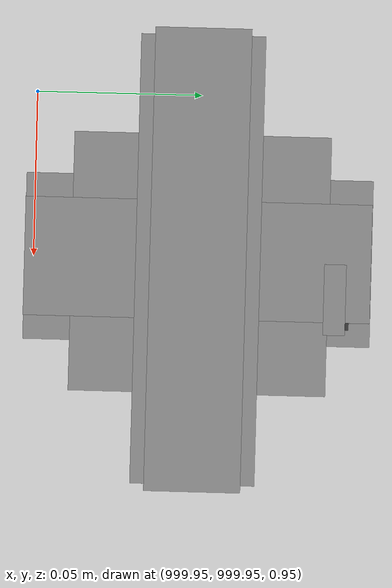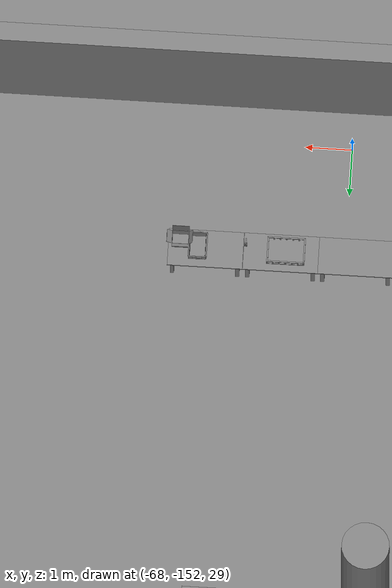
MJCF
<mujoco>
    <option gravity="0.000000000 0.000000000 -9.810000420" timestep="0.0049999999" integrator="implicitfast" density="1.225" viscosity="1.8000001e-05" noslip_iterations="10" iterations="100" sdf_iterations="50">
        <flag multiccd="disable"/>
    </option>
    <size memory="1000M"/>
    <compiler coordinate="local"/>
    <worldbody>
        <light cutoff="30" pos="0 1 1" dir="0 -1 -2"/>
        <light cutoff="30" pos="0 -1 1" dir="0 1 -2"/>
        <body pos="-66.319999695 -149.108520508 31.170557022" euler="-149.060348511 75.514991760 66.365341187" mocap="true" name="spotlight5_SpotLight"/>
        <body pos="1000.000000000 1000.000000000 1.000000000" euler="0.000011953 0.000005123 -179.999984741" name="openloong_gripper_2f85_fix_base_usda_intel_box">
            <geom contype="1" conaffinity="1" density="1000" type="box" material="" rgba="0.500000000 0.500000000 0.500000000 1.000000000" solimp="0.899999976 0.949999988 0.001000000" friction="1.000000000 0.005000000 0.000100000" solref="0.020000000 1.000000000" margin="0" condim="3" group="0" pos="0.000000000 -0.000067139 0.000082284" quat="0.707106709 0.000000225 0.000000253 0.707106650" size="0.052800003 0.025300000 0.052800003" name="openloong_gripper_2f85_fix_base_usda_geom_62A10FE0_2FC2_413E_A1F2_4E7C3F5A4804"/>
            <freejoint name="openloong_gripper_2f85_fix_base_usda_intel_box_joint"/>
            <site size="0.005000000 0.005000000 0.005000000" rgba="0.500000000 0.500000000 0.500000000 1.000000000" pos="0.000000000 0.000000000 0.000000000" quat="0.999961913 0.008726500 0.000000000 0.000000000" group="0" type="sphere" name="openloong_gripper_2f85_fix_base_usda_intel_boxsite"/>
        </body>
        <body pos="1000.000000000 1000.000000000 1.000000000" euler="0.000000000 0.000000000 180.000000000" name="openloong_gripper_2f85_fix_base_usda_cpu_fan">
            <geom contype="1" conaffinity="1" density="1000" type="box" material="" rgba="0.500000000 0.500000000 0.500000000 1.000000000" solimp="0.899999976 0.949999988 0.001000000" friction="1.000000000 0.005000000 0.000100000" solref="0.020000000 1.000000000" margin="0" condim="3" group="0" pos="0.000000000 0.000000000 0.070034981" quat="0.000000000 0.000000000 0.000000000 1.000000000" size="0.070700005 0.014699999 0.070700005" name="openloong_gripper_2f85_fix_base_usda_geom_62BE3CD1_99F1_485B_A863_0F0A01B70939"/>
            <freejoint name="openloong_gripper_2f85_fix_base_usda_cpu_fan_joint"/>
            <site size="0.005000000 0.005000000 0.005000000" rgba="0.500000000 0.500000000 0.500000000 1.000000000" pos="0.000000000 0.000000000 0.000000000" quat="0.999961913 0.008726535 0.000000000 0.000000000" group="0" type="sphere" name="openloong_gripper_2f85_fix_base_usda_cpu_fancsite"/>
        </body>
        <body pos="1000.000000000 1000.000000000 1.000000000" euler="0.000000000 0.000000000 180.000000000" name="openloong_gripper_2f85_fix_base_usda_battery_01">
            <geom contype="1" conaffinity="1" density="1000" type="box" material="" rgba="0.500000000 0.500000000 0.500000000 1.000000000" solimp="0.899999976 0.949999988 0.001000000" friction="1.000000000 0.005000000 0.000100000" solref="0.020000000 1.000000000" margin="0" condim="3" group="0" pos="-0.011123657 -0.041940309 0.101691343" quat="1.000000000 0.000000000 0.000000000 0.000000000" size="0.010800000 0.003375000 0.004725000" name="openloong_gripper_2f85_fix_base_usda_geom_904430F6_8B6C_4FBC_ABEA_4181E5420F51"/>
            <geom contype="1" conaffinity="1" density="1000" type="box" material="" rgba="0.500000000 0.500000000 0.500000000 1.000000000" solimp="0.899999976 0.949999988 0.001000000" friction="1.000000000 0.005000000 0.000100000" solref="0.020000000 1.000000000" margin="0" condim="3" group="0" pos="-0.010876465 -0.044247437 0.047066893" quat="0.998702705 -0.050920475 0.000000000 0.000000000" size="0.009450001 0.002700000 0.024975000" name="openloong_gripper_2f85_fix_base_usda_geom_C81A11BD_6A86_409A_9B68_A0C898D05541"/>
            <geom contype="1" conaffinity="1" density="1000" type="box" material="" rgba="0.500000000 0.500000000 0.500000000 1.000000000" solimp="0.899999976 0.949999988 0.001000000" friction="1.000000000 0.005000000 0.000100000" solref="0.020000000 1.000000000" margin="0" condim="3" group="0" pos="-0.001235962 -0.000659180 0.047381196" quat="1.000000000 0.000000000 0.000000000 0.000000000" size="0.039420001 0.039150000 0.047250003" name="openloong_gripper_2f85_fix_base_usda_geom_F4583065_1C5D_4ACE_BE43_A9491347FC29"/>
            <geom contype="1" conaffinity="1" density="1000" type="box" material="" rgba="0.500000000 0.500000000 0.500000000 1.000000000" solimp="0.899999976 0.949999988 0.001000000" friction="1.000000000 0.005000000 0.000100000" solref="0.020000000 1.000000000" margin="0" condim="3" group="0" pos="-0.010876465 -0.039138794 0.009851727" quat="1.000000000 0.000000000 0.000000000 0.000000000" size="0.009450001 0.010800000 0.013500000" name="openloong_gripper_2f85_fix_base_usda_geom_D99A0A3C_E6F9_4DC0_8DC3_3B095580D7AF"/>
            <geom contype="1" conaffinity="1" density="1000" type="box" material="" rgba="0.500000000 0.500000000 0.500000000 1.000000000" solimp="0.899999976 0.949999988 0.001000000" friction="1.000000000 0.005000000 0.000100000" solref="0.020000000 1.000000000" margin="0" condim="3" group="0" pos="-0.010876465 -0.041528322 0.071508206" quat="1.000000000 0.000000000 0.000000000 0.000000000" size="0.009450001 0.002700000 0.027000001" name="openloong_gripper_2f85_fix_base_usda_geom_7A84DC95_EA7E_49B7_AEB1_63327EE159BE"/>
            <freejoint name="openloong_gripper_2f85_fix_base_usda_battery_01_joint"/>
            <site size="0.005000000 0.005000000 0.005000000" rgba="0.500000000 0.500000000 0.500000000 1.000000000" pos="0.000000000 0.000000000 0.000000000" quat="0.999961913 0.008726500 0.000000000 0.000000000" group="0" type="sphere" name="openloong_gripper_2f85_fix_base_usda_battery_01site"/>
        </body>
        <body pos="1000.000000000 1000.000000000 1.000000000" euler="0.000000000 0.000000000 180.000000000" name="openloong_gripper_2f85_fix_base_usda_wifi_box">
            <geom contype="1" conaffinity="1" density="1000" type="box" material="" rgba="0.500000000 0.500000000 0.500000000 1.000000000" solimp="0.899999976 0.949999988 0.001000000" friction="1.000000000 0.005000000 0.000100000" solref="0.020000000 1.000000000" margin="0" condim="3" group="0" pos="0.000000000 0.000000000 0.058978677" quat="0.000000000 0.000000047 0.000000000 1.000000000" size="0.068499997 0.018999999 0.059000000" name="openloong_gripper_2f85_fix_base_usda_geom_B6D5BDB9_E808_4144_9138_4C6C2308B496"/>
            <freejoint name="openloong_gripper_2f85_fix_base_usda_wifi_box_joint"/>
            <site size="0.005000000 0.005000000 0.005000000" rgba="0.500000000 0.500000000 0.500000000 1.000000000" pos="0.000000000 0.000000000 0.000000000" quat="0.999961913 0.008726500 0.000000000 0.000000000" group="0" type="sphere" name="openloong_gripper_2f85_fix_base_usda_wifi_boxsite"/>
        </body>
        <body pos="1000.000000000 999.999938965 1.000000000" euler="0.000000000 0.000000000 180.000000000" name="openloong_gripper_2f85_fix_base_usda_intelcore_i5">
            <geom contype="1" conaffinity="1" density="1000" type="box" material="" rgba="0.500000000 0.500000000 0.500000000 1.000000000" solimp="0.899999976 0.949999988 0.001000000" friction="1.000000000 0.005000000 0.000100000" solref="0.020000000 1.000000000" margin="0" condim="3" group="0" pos="0.000000000 0.000000000 0.051722717" quat="0.707106709 0.000000000 0.000000000 -0.707106769" size="0.052800000 0.018080002 0.052800000" name="openloong_gripper_2f85_fix_base_usda_geom_F89E1154_793D_4282_82E2_B9EF9266728B"/>
            <freejoint name="openloong_gripper_2f85_fix_base_usda_intelcore_i5_joint"/>
            <site size="0.005000000 0.005000000 0.005000000" rgba="0.500000000 0.500000000 0.500000000 1.000000000" pos="0.000000000 0.000000000 0.000000000" quat="0.999961913 0.008726534 0.000000000 0.000000000" group="0" type="sphere" name="openloong_gripper_2f85_fix_base_usda_intelcore_i5site"/>
        </body>
        <body pos="-66.325218201 -149.516189575 31.166202545" euler="60.996017456 52.832366943 -21.951536179" mocap="true" name="spotlight1_SpotLight"/>
        <body pos="-66.288619995 -149.401702881 31.167617798" euler="13.010102272 24.098693848 -161.405685425" mocap="true" name="spotlight4_SpotLight"/>
        <body pos="-64.866622925 -149.383972168 30.183746338" euler="89.999984741 89.999946594 0.000000000" name="openloong_gripper_2f85_fix_base_usda_bluebox_01">
            <geom contype="1" conaffinity="1" density="1000" type="box" material="" rgba="0.500000000 0.500000000 0.500000000 1.000000000" solimp="0.899999976 0.949999988 0.001000000" friction="1.000000000 0.005000000 0.000100000" solref="0.020000000 1.000000000" margin="0" condim="3" group="0" pos="0.276580811 0.187225342 0.000068665" quat="0.707106948 0.000077471 0.707106352 0.000077486" size="0.100000001 0.057999998 0.010000000" name="openloong_gripper_2f85_fix_base_usda_geom_D2FACEF7_7B03_4BAB_BD1A_20F3C253921E"/>
            <geom contype="1" conaffinity="1" density="1000" type="box" material="" rgba="0.500000000 0.500000000 0.500000000 1.000000000" solimp="0.899999976 0.949999988 0.001000000" friction="1.000000000 0.005000000 0.000100000" solref="0.020000000 1.000000000" margin="0" condim="3" group="0" pos="0.000000000 0.002883911 0.000000000" quat="0.999999881 0.000000000 0.000000000 0.000000000" size="0.254000008 0.003000000 0.172000006" name="openloong_gripper_2f85_fix_base_usda_geom_31BDA4AF_B0B8_4C4A_8D02_E1E38D85E628"/>
            <geom contype="1" conaffinity="1" density="1000" type="box" material="" rgba="0.500000000 0.500000000 0.500000000 1.000000000" solimp="0.899999976 0.949999988 0.001000000" friction="1.000000000 0.005000000 0.000100000" solref="0.020000000 1.000000000" margin="0" condim="3" group="0" pos="0.000000000 0.124874115 0.173484802" quat="0.999796331 0.020176515 -0.000000015 0.000000030" size="0.259999990 0.119999997 0.007000000" name="openloong_gripper_2f85_fix_base_usda_geom_99DE47B8_BE16_4279_9D1E_94B3AEDB7297"/>
            <geom contype="1" conaffinity="1" density="1000" type="box" material="" rgba="0.500000000 0.500000000 0.500000000 1.000000000" solimp="0.899999976 0.949999988 0.001000000" friction="1.000000000 0.005000000 0.000100000" solref="0.020000000 1.000000000" margin="0" condim="3" group="0" pos="0.000000000 0.124874115 -0.173469543" quat="0.999796331 -0.020176545 -0.000000015 0.000000000" size="0.259999990 0.119999997 0.007000000" name="openloong_gripper_2f85_fix_base_usda_geom_4D797EF7_B7E9_4561_9AF4_7E8D942FC6CA"/>
            <geom contype="1" conaffinity="1" density="1000" type="box" material="" rgba="0.500000000 0.500000000 0.500000000 1.000000000" solimp="0.899999976 0.949999988 0.001000000" friction="1.000000000 0.005000000 0.000100000" solref="0.020000000 1.000000000" margin="0" condim="3" group="0" pos="0.000000000 0.214008331 0.188980103" quat="0.999912977 0.013176724 0.000000015 0.000000000" size="0.259999990 0.029999999 0.012500000" name="openloong_gripper_2f85_fix_base_usda_geom_AD9F1D5B_1082_4778_996D_D6B5E20E0A71"/>
            <geom contype="1" conaffinity="1" density="1000" type="box" material="" rgba="0.500000000 0.500000000 0.500000000 1.000000000" solimp="0.899999976 0.949999988 0.001000000" friction="1.000000000 0.005000000 0.000100000" solref="0.020000000 1.000000000" margin="0" condim="3" group="0" pos="-0.258361816 0.125289917 0.001876831" quat="0.702796936 -0.020792112 0.710783124 0.020769298" size="0.189999998 0.119999997 0.009000000" name="openloong_gripper_2f85_fix_base_usda_geom_77D8AD39_6B6D_41EF_A9BE_CCF45C0BFA31"/>
            <geom contype="1" conaffinity="1" density="1000" type="box" material="" rgba="0.500000000 0.500000000 0.500000000 1.000000000" solimp="0.899999976 0.949999988 0.001000000" friction="1.000000000 0.005000000 0.000100000" solref="0.020000000 1.000000000" margin="0" condim="3" group="0" pos="0.000000000 0.214008331 -0.188980103" quat="0.999912977 -0.013176769 0.000000030 0.000000015" size="0.259999990 0.029999999 0.012500000" name="openloong_gripper_2f85_fix_base_usda_geom_41132920_9F87_4BDB_A6A5_4B307A302649"/>
            <geom contype="1" conaffinity="1" density="1000" type="box" material="" rgba="0.500000000 0.500000000 0.500000000 1.000000000" solimp="0.899999976 0.949999988 0.001000000" friction="1.000000000 0.005000000 0.000100000" solref="0.020000000 1.000000000" margin="0" condim="3" group="0" pos="-0.276611328 0.187225342 0.000068665" quat="0.707106650 0.000077441 0.707106709 0.000077456" size="0.100000001 0.057999998 0.010000000" name="openloong_gripper_2f85_fix_base_usda_geom_88DBB396_4FF1_41C5_823A_C59699CC55FE"/>
            <geom contype="1" conaffinity="1" density="1000" type="box" material="" rgba="0.500000000 0.500000000 0.500000000 1.000000000" solimp="0.899999976 0.949999988 0.001000000" friction="1.000000000 0.005000000 0.000100000" solref="0.020000000 1.000000000" margin="0" condim="3" group="0" pos="0.258331299 0.125289917 0.001876831" quat="0.702851415 0.018856421 0.710823774 -0.019329369" size="0.189999998 0.119999997 0.009000000" name="openloong_gripper_2f85_fix_base_usda_geom_DC09C94B_43FB_4EE4_8410_4050267DEF86"/>
            <freejoint name="openloong_gripper_2f85_fix_base_usda_bluebox_01_joint"/>
            <site size="0.005000000 0.005000000 0.005000000" rgba="0.500000000 0.500000000 0.500000000 1.000000000" pos="0.000000000 0.000000000 0.000000000" quat="0.999961913 0.008726534 0.000000000 0.000000000" group="0" type="sphere" name="openloong_gripper_2f85_fix_base_usda_bluebox_01site"/>
        </body>
        <body pos="-64.496299744 -149.491867065 30.235729218" euler="0.000000000 0.000000000 89.999946594" name="openloong_gripper_2f85_fix_base_usda_cardboardbox_01">
            <geom contype="1" conaffinity="1" density="1000" type="box" material="" rgba="0.500000000 0.500000000 0.500000000 1.000000000" solimp="0.899999976 0.949999988 0.001000000" friction="1.000000000 0.005000000 0.000100000" solref="0.020000000 1.000000000" margin="0" condim="3" group="0" pos="-0.003166199 -0.004086494 0.005052090" quat="1.000000000 0.000000000 0.000000000 0.000000000" size="0.142499998 0.177500010 0.005000000" name="openloong_gripper_2f85_fix_base_usda_geom_C77900CC_05B8_40B2_951D_D0EF44B67F43"/>
            <geom contype="1" conaffinity="1" density="1000" type="box" material="" rgba="0.500000000 0.500000000 0.500000000 1.000000000" solimp="0.899999976 0.949999988 0.001000000" friction="1.000000000 0.005000000 0.000100000" solref="0.020000000 1.000000000" margin="0" condim="3" group="0" pos="-0.003166199 0.170316696 0.150570869" quat="1.000000000 0.000000000 0.000000000 0.000000000" size="0.142499998 0.005000000 0.149999991" name="openloong_gripper_2f85_fix_base_usda_geom_F6EF729D_1649_4D57_9227_80FCBB19AF0F"/>
            <geom contype="1" conaffinity="1" density="1000" type="box" material="" rgba="0.500000000 0.500000000 0.500000000 1.000000000" solimp="0.899999976 0.949999988 0.001000000" friction="1.000000000 0.005000000 0.000100000" solref="0.020000000 1.000000000" margin="0" condim="3" group="0" pos="-0.147399902 -0.005307198 0.150570869" quat="1.000000000 0.000000000 0.000000000 0.000000000" size="0.005000000 0.177500010 0.149999991" name="openloong_gripper_2f85_fix_base_usda_geom_93B7D8B3_F22A_4241_B3DB_C4292FF400C9"/>
            <geom contype="1" conaffinity="1" density="1000" type="box" material="" rgba="0.500000000 0.500000000 0.500000000 1.000000000" solimp="0.899999976 0.949999988 0.001000000" friction="1.000000000 0.005000000 0.000100000" solref="0.020000000 1.000000000" margin="0" condim="3" group="0" pos="0.140275955 -0.005307198 0.150570869" quat="1.000000000 0.000000000 0.000000000 0.000000000" size="0.005000000 0.177500010 0.149999991" name="openloong_gripper_2f85_fix_base_usda_geom_09D6F0B8_1150_4EA9_B82B_D896801B3789"/>
            <geom contype="1" conaffinity="1" density="1000" type="box" material="" rgba="0.500000000 0.500000000 0.500000000 1.000000000" solimp="0.899999976 0.949999988 0.001000000" friction="1.000000000 0.005000000 0.000100000" solref="0.020000000 1.000000000" margin="0" condim="3" group="0" pos="-0.003166199 -0.181550980 0.150570869" quat="1.000000000 0.000000000 0.000000000 0.000000000" size="0.142499998 0.005000000 0.149999991" name="openloong_gripper_2f85_fix_base_usda_geom_E92BD5E9_93F0_4BF9_BEFA_E86245FD05F9"/>
            <freejoint name="openloong_gripper_2f85_fix_base_usda_cardboardbox_01_joint"/>
            <site size="0.005000000 0.005000000 0.005000000" rgba="0.500000000 0.500000000 0.500000000 1.000000000" pos="0.000000000 0.000000000 0.000000000" quat="0.999961913 0.008726535 0.000000000 0.000000000" group="0" type="sphere" name="openloong_gripper_2f85_fix_base_usda_site_2FA2F744_EA96_4D97_80D8_333AD1DFBCB0"/>
            <body pos="0.139160156 -0.004048347 0.301930904" euler="-179.999954224 49.383502960 179.999954224" name="openloong_gripper_2f85_fix_base_usda_A1_006">
                <geom contype="1" conaffinity="1" density="1000" type="box" material="" rgba="0.500000000 0.500000000 0.500000000 1.000000000" solimp="0.899999976 0.949999988 0.001000000" friction="1.000000000 0.005000000 0.000100000" solref="0.020000000 1.000000000" margin="0" condim="3" group="0" pos="-0.071587563 0.000009537 0.001745224" quat="0.999999881 0.000000000 0.000000000 0.000000000" size="0.071249999 0.179999992 0.002500000" name="openloong_gripper_2f85_fix_base_usda_geom_3FDFFC57_899C_4534_9C9F_8BE801B0D812"/>
                <joint armature="0" stiffness="0.07" damping="0.0099999998" axis="0.000000 1.000000 0.000000" type="hinge" name="openloong_gripper_2f85_fix_base_usda_A1_006"/>
            </body>
            <body pos="-0.145902634 -0.004086494 0.301938057" euler="-180.000000000 -60.000011444 -180.000000000" name="openloong_gripper_2f85_fix_base_usda_A2_006">
                <geom contype="1" conaffinity="1" density="1000" type="box" material="" rgba="0.500000000 0.500000000 0.500000000 1.000000000" solimp="0.899999976 0.949999988 0.001000000" friction="1.000000000 0.005000000 0.000100000" solref="0.020000000 1.000000000" margin="0" condim="3" group="0" pos="0.071268082 0.000009537 0.002717972" quat="0.000002921 0.000000000 -0.000000030 0.999999881" size="0.071249999 0.179999992 0.002500000" name="openloong_gripper_2f85_fix_base_usda_geom_1CFAC864_4454_4630_81E9_1C085D3E2E77"/>
                <joint armature="0" stiffness="0.07" damping="0.0099999998" axis="0.000000 1.000000 0.000000" type="hinge" name="openloong_gripper_2f85_fix_base_usda_A2_006"/>
            </body>
            <body pos="-0.003385544 0.175991058 0.301930904" euler="-125.858116150 -0.000004561 0.000002331" name="openloong_gripper_2f85_fix_base_usda_B2_006">
                <geom contype="1" conaffinity="1" density="1000" type="box" material="" rgba="0.500000000 0.500000000 0.500000000 1.000000000" solimp="0.899999976 0.949999988 0.001000000" friction="1.000000000 0.005000000 0.000100000" solref="0.020000000 1.000000000" margin="0" condim="3" group="0" pos="0.000009537 -0.070939064 -0.002470016" quat="0.999614120 0.027776197 -0.000000015 0.000000030" size="0.137500003 0.064999998 0.005000000" name="openloong_gripper_2f85_fix_base_usda_geom_A577C0C8_1001_4041_BE0E_1955DABDE4C5"/>
                <joint armature="0" stiffness="0.07" damping="0.0099999998" axis="1.000000 0.000000 0.000000" type="hinge" name="openloong_gripper_2f85_fix_base_usda_B2_006"/>
            </body>
            <body pos="-0.003385544 -0.184140205 0.301938057" euler="147.805557251 0.000000000 0.000000000" name="openloong_gripper_2f85_fix_base_usda_B1_006">
                <geom contype="1" conaffinity="1" density="1000" type="box" material="" rgba="0.500000000 0.500000000 0.500000000 1.000000000" solimp="0.899999976 0.949999988 0.001000000" friction="1.000000000 0.005000000 0.000100000" solref="0.020000000 1.000000000" margin="0" condim="3" group="0" pos="-0.000028610 0.070202351 -0.002703667" quat="0.999614179 -0.027776167 0.000000000 0.000000000" size="0.137500003 0.064999998 0.005000000" name="openloong_gripper_2f85_fix_base_usda_geom_8D53AB95_655F_46F5_9F89_7FF85436537A"/>
                <joint armature="0" stiffness="0.07" damping="0.0099999998" axis="1.000000 0.000000 0.000000" type="hinge" name="openloong_gripper_2f85_fix_base_usda_B1_006"/>
            </body>
        </body>
        <body pos="-65.882858276 -149.481979370 30.229999542" euler="-64.487716675 0.000000000 0.000000000" name="openloong_gripper_2f85_fix_base_usda_Barcode">
            <geom contype="1" conaffinity="1" density="1000" type="box" material="" rgba="0.500000000 0.500000000 0.500000000 1.000000000" solimp="0.899999976 0.949999988 0.001000000" friction="1.000000000 0.005000000 0.000100000" solref="0.020000000 1.000000000" margin="0" condim="3" group="0" pos="0.000000000 0.013038635 0.001419067" quat="0.000000000 0.000000000 0.000000000 1.000000119" size="0.034000002 0.010000000 0.017999999" name="openloong_gripper_2f85_fix_base_usda_geom_412305FA_311D_4B21_99F8_15ABC9BB7595"/>
            <geom contype="1" conaffinity="1" density="1000" type="box" material="" rgba="0.500000000 0.500000000 0.500000000 1.000000000" solimp="0.899999976 0.949999988 0.001000000" friction="1.000000000 0.005000000 0.000100000" solref="0.020000000 1.000000000" margin="0" condim="3" group="0" pos="0.000000000 -0.035301208 -0.007095337" quat="0.000000000 0.000000000 -0.043619365 0.999048233" size="0.028999999 0.010000000 0.020000000" name="openloong_gripper_2f85_fix_base_usda_geom_F2BD8E94_B87F_4D1E_9650_A6745EAE9DD2"/>
            <geom contype="1" conaffinity="1" density="1000" type="box" material="" rgba="0.500000000 0.500000000 0.500000000 1.000000000" solimp="0.899999976 0.949999988 0.001000000" friction="1.000000000 0.005000000 0.000100000" solref="0.020000000 1.000000000" margin="0" condim="3" group="0" pos="0.000000000 -0.043411255 -0.011749268" quat="0.922262907 0.386563420 0.000000000 0.000000000" size="0.026000001 0.010000000 0.020000000" name="openloong_gripper_2f85_fix_base_usda_geom_566EDE13_8EBE_40CE_AC57_8B573E84E57C"/>
            <geom contype="1" conaffinity="1" density="1000" type="box" material="" rgba="0.500000000 0.500000000 0.500000000 1.000000000" solimp="0.899999976 0.949999988 0.001000000" friction="1.000000000 0.005000000 0.000100000" solref="0.020000000 1.000000000" margin="0" condim="3" group="0" pos="0.000000000 -0.016967773 -0.031860352" quat="0.000000000 0.000000000 0.000000000 1.000000119" size="0.008000000 0.010000000 0.013000000" name="openloong_gripper_2f85_fix_base_usda_geom_AC818BA8_C7E1_424D_BC78_F9A5D008BB00"/>
            <geom contype="1" conaffinity="1" density="1000" type="box" material="" rgba="0.500000000 0.500000000 0.500000000 1.000000000" solimp="0.899999976 0.949999988 0.001000000" friction="1.000000000 0.005000000 0.000100000" solref="0.020000000 1.000000000" margin="0" condim="3" group="0" pos="0.000000000 -0.001869202 0.000312805" quat="0.953716993 0.300705761 0.000000000 0.000000000" size="0.032000002 0.010000000 0.018999999" name="openloong_gripper_2f85_fix_base_usda_geom_012A6E0A_47DA_4B90_AF64_6FF2EB5740C5"/>
            <geom contype="1" conaffinity="1" density="1000" type="box" material="" rgba="0.500000000 0.500000000 0.500000000 1.000000000" solimp="0.899999976 0.949999988 0.001000000" friction="1.000000000 0.005000000 0.000100000" solref="0.020000000 1.000000000" margin="0" condim="3" group="0" pos="0.000000000 -0.019531250 -0.003173828" quat="0.953716993 0.300705761 0.000000000 0.000000000" size="0.030999999 0.010000000 0.020000000" name="openloong_gripper_2f85_fix_base_usda_geom_3DFA253C_37C7_40C8_B618_4756088629EF"/>
            <geom contype="1" conaffinity="1" density="1000" type="box" material="" rgba="0.500000000 0.500000000 0.500000000 1.000000000" solimp="0.899999976 0.949999988 0.001000000" friction="1.000000000 0.005000000 0.000100000" solref="0.020000000 1.000000000" margin="0" condim="3" group="0" pos="0.000000000 -0.035301208 -0.007095337" quat="0.953716993 0.300705761 0.000000000 0.000000000" size="0.028999999 0.010000000 0.020000000" name="openloong_gripper_2f85_fix_base_usda_geom_747F338E_D393_449E_AAF4_3A815EF2AF69"/>
            <geom contype="1" conaffinity="1" density="1000" type="box" material="" rgba="0.500000000 0.500000000 0.500000000 1.000000000" solimp="0.899999976 0.949999988 0.001000000" friction="1.000000000 0.005000000 0.000100000" solref="0.020000000 1.000000000" margin="0" condim="3" group="0" pos="0.000000000 -0.042617798 -0.071121216" quat="0.000000000 0.000000000 0.000000000 1.000000119" size="0.013000000 0.021000000 0.059999999" name="openloong_gripper_2f85_fix_base_usda_geom_F7F63516_6928_4159_8DB8_9A35033E90C0"/>
            <freejoint name="openloong_gripper_2f85_fix_base_usda_Barcode_joint"/>
            <site size="0.005000000 0.005000000 0.005000000" rgba="0.500000000 0.500000000 0.500000000 1.000000000" pos="0.000000000 0.000000000 0.000000000" quat="1.000000000 0.000000000 0.000000000 0.000000000" group="0" type="sphere" name="openloong_gripper_2f85_fix_base_usda_Barcode_site"/>
        </body>
        <body pos="-66.745018005 -149.392349243 30.184000015" euler="0.000000000 0.000000000 89.999946594" name="[22331634693626]_Basket_01">
            <geom contype="1" conaffinity="1" density="1000" type="box" material="" rgba="0.500000000 0.500000000 0.500000000 1.000000000" solimp="0.899999976 0.949999988 0.001000000" friction="1.000000000 0.005000000 0.000100000" solref="0.020000000 1.000000000" margin="0" condim="3" group="0" pos="-0.052425385 0.389207840 0.089787483" quat="0.707107008 0.000000000 0.000000000 0.707106411" size="0.014249999 0.014249999 0.059999999" name="[22331634693626]_geom_7165F0A5_82EF_4895_9054_6642DA55579C"/>
            <geom contype="1" conaffinity="1" density="1000" type="box" material="" rgba="0.500000000 0.500000000 0.500000000 1.000000000" solimp="0.899999976 0.949999988 0.001000000" friction="1.000000000 0.005000000 0.000100000" solref="0.020000000 1.000000000" margin="0" condim="3" group="0" pos="0.264015198 -0.133043289 0.089787483" quat="0.707107008 0.000000000 0.000000000 0.707106411" size="0.014249999 0.014249999 0.059999999" name="[22331634693626]_geom_6FA1C884_CB83_47A4_92B3_391789A4F4F8"/>
            <geom contype="1" conaffinity="1" density="1000" type="box" material="" rgba="0.500000000 0.500000000 0.500000000 1.000000000" solimp="0.899999976 0.949999988 0.001000000" friction="1.000000000 0.005000000 0.000100000" solref="0.020000000 1.000000000" margin="0" condim="3" group="0" pos="-0.264015198 -0.265548706 0.089793205" quat="0.707107008 0.000000000 0.000000000 0.707106411" size="0.014249999 0.014249999 0.059999999" name="[22331634693626]_geom_E9D1F3F3_ADAF_4849_8882_1BA8567B2E31"/>
            <geom contype="1" conaffinity="1" density="1000" type="box" material="" rgba="0.500000000 0.500000000 0.500000000 1.000000000" solimp="0.899999976 0.949999988 0.001000000" friction="1.000000000 0.005000000 0.000100000" solref="0.020000000 1.000000000" margin="0" condim="3" group="0" pos="-0.160263062 -0.389322281 0.089793205" quat="0.707107008 0.000000000 0.000000000 0.707106411" size="0.014249999 0.014249999 0.059999999" name="[22331634693626]_geom_4D6A1050_3949_458E_988D_30FF42BAED40"/>
            <geom contype="1" conaffinity="1" density="1000" type="box" material="" rgba="0.500000000 0.500000000 0.500000000 1.000000000" solimp="0.899999976 0.949999988 0.001000000" friction="1.000000000 0.005000000 0.000100000" solref="0.020000000 1.000000000" margin="0" condim="3" group="0" pos="0.162265778 -0.389322281 0.089787483" quat="0.707107008 0.000000000 0.000000000 0.707106411" size="0.014249999 0.014249999 0.059999999" name="[22331634693626]_geom_E8EDC1E9_FE3A_4957_A7CE_68ACCB99932E"/>
            <geom contype="1" conaffinity="1" density="1000" type="box" material="" rgba="0.500000000 0.500000000 0.500000000 1.000000000" solimp="0.899999976 0.949999988 0.001000000" friction="1.000000000 0.005000000 0.000100000" solref="0.020000000 1.000000000" margin="0" condim="3" group="0" pos="0.264015198 0.389207840 0.089787483" quat="0.707107008 0.000000000 0.000000000 0.707106411" size="0.014249999 0.014249999 0.059999999" name="[22331634693626]_geom_1920BBB2_2209_4577_B6AF_A63D4F53E0D9"/>
            <geom contype="1" conaffinity="1" density="1000" type="box" material="" rgba="0.500000000 0.500000000 0.500000000 1.000000000" solimp="0.899999976 0.949999988 0.001000000" friction="1.000000000 0.005000000 0.000100000" solref="0.020000000 1.000000000" margin="0" condim="3" group="0" pos="-0.264015198 -0.133043289 0.089793205" quat="0.707107008 0.000000000 0.000000000 0.707106411" size="0.014249999 0.014249999 0.059999999" name="[22331634693626]_geom_77F67102_CCEC_4856_B03B_870EC478C93C"/>
            <geom contype="1" conaffinity="1" density="1000" type="box" material="" rgba="0.500000000 0.500000000 0.500000000 1.000000000" solimp="0.899999976 0.949999988 0.001000000" friction="1.000000000 0.005000000 0.000100000" solref="0.020000000 1.000000000" margin="0" condim="3" group="0" pos="-0.264026642 0.269256592 0.089793205" quat="0.707107008 0.000000000 0.000000000 0.707106411" size="0.014249999 0.014249999 0.059999999" name="[22331634693626]_geom_1655F49D_F800_4670_BE8F_826630EADDCE"/>
            <geom contype="1" conaffinity="1" density="1000" type="box" material="" rgba="0.500000000 0.500000000 0.500000000 1.000000000" solimp="0.899999976 0.949999988 0.001000000" friction="1.000000000 0.005000000 0.000100000" solref="0.020000000 1.000000000" margin="0" condim="3" group="0" pos="0.054462433 0.389207840 0.089787483" quat="0.707107008 0.000000000 0.000000000 0.707106411" size="0.014249999 0.014249999 0.059999999" name="[22331634693626]_geom_41F856C0_E2C4_4B2D_B472_781473C97AA1"/>
            <geom contype="1" conaffinity="1" density="1000" type="box" material="" rgba="0.500000000 0.500000000 0.500000000 1.000000000" solimp="0.899999976 0.949999988 0.001000000" friction="1.000000000 0.005000000 0.000100000" solref="0.020000000 1.000000000" margin="0" condim="3" group="0" pos="0.054462433 -0.389322281 0.089787483" quat="0.707107008 0.000000000 0.000000000 0.707106411" size="0.014249999 0.014249999 0.059999999" name="[22331634693626]_geom_EE126557_4503_4EE8_B1F4_2D407563CBA2"/>
            <geom contype="1" conaffinity="1" density="1000" type="box" material="" rgba="0.500000000 0.500000000 0.500000000 1.000000000" solimp="0.899999976 0.949999988 0.001000000" friction="1.000000000 0.005000000 0.000100000" solref="0.020000000 1.000000000" margin="0" condim="3" group="0" pos="0.264015198 0.269256592 0.089793205" quat="0.707107008 0.000000000 0.000000000 0.707106411" size="0.014249999 0.014249999 0.059999999" name="[22331634693626]_geom_BEA2C7D7_6868_4F55_9CCB_05BC78871DA6"/>
            <geom contype="1" conaffinity="1" density="1000" type="box" material="" rgba="0.500000000 0.500000000 0.500000000 1.000000000" solimp="0.899999976 0.949999988 0.001000000" friction="1.000000000 0.005000000 0.000100000" solref="0.020000000 1.000000000" margin="0" condim="3" group="0" pos="0.264015198 -0.389322281 0.089787483" quat="0.707107008 0.000000000 0.000000000 0.707106411" size="0.014249999 0.014249999 0.059999999" name="[22331634693626]_geom_9E092B70_636F_4D47_8C41_29DE6EA1F066"/>
            <geom contype="1" conaffinity="1" density="1000" type="box" material="" rgba="0.500000000 0.500000000 0.500000000 1.000000000" solimp="0.899999976 0.949999988 0.001000000" friction="1.000000000 0.005000000 0.000100000" solref="0.020000000 1.000000000" margin="0" condim="3" group="0" pos="0.000000000 0.000000000 0.015998840" quat="0.707107008 0.000000000 0.000000000 0.707106411" size="0.403499991 0.279000014 0.015750000" name="[22331634693626]_geom_44395931_103B_4658_ABD3_1CC6509C72FA"/>
            <geom contype="1" conaffinity="1" density="1000" type="box" material="" rgba="0.500000000 0.500000000 0.500000000 1.000000000" solimp="0.899999976 0.949999988 0.001000000" friction="1.000000000 0.005000000 0.000100000" solref="0.020000000 1.000000000" margin="0" condim="3" group="0" pos="0.000000000 -0.389476776 0.163619041" quat="0.707107008 0.000000000 0.000000000 0.707106411" size="0.015000000 0.277500004 0.015750000" name="[22331634693626]_geom_3678FA48_24BC_4F70_81BC_6B1AE7B743A1"/>
            <geom contype="1" conaffinity="1" density="1000" type="box" material="" rgba="0.500000000 0.500000000 0.500000000 1.000000000" solimp="0.899999976 0.949999988 0.001000000" friction="1.000000000 0.005000000 0.000100000" solref="0.020000000 1.000000000" margin="0" condim="3" group="0" pos="0.162265778 0.389207840 0.089787483" quat="0.707107008 0.000000000 0.000000000 0.707106411" size="0.014249999 0.014249999 0.059999999" name="[22331634693626]_geom_4E17C263_EA7C_4B7F_ABDB_CAF499A59924"/>
            <geom contype="1" conaffinity="1" density="1000" type="box" material="" rgba="0.500000000 0.500000000 0.500000000 1.000000000" solimp="0.899999976 0.949999988 0.001000000" friction="1.000000000 0.005000000 0.000100000" solref="0.020000000 1.000000000" margin="0" condim="3" group="0" pos="0.000000000 0.389471054 0.163619041" quat="0.707107008 0.000000000 0.000000000 0.707106411" size="0.015000000 0.277500004 0.015750000" name="[22331634693626]_geom_CCE1882F_DA83_493D_8C4C_21BEBCDC558F"/>
            <geom contype="1" conaffinity="1" density="1000" type="box" material="" rgba="0.500000000 0.500000000 0.500000000 1.000000000" solimp="0.899999976 0.949999988 0.001000000" friction="1.000000000 0.005000000 0.000100000" solref="0.020000000 1.000000000" margin="0" condim="3" group="0" pos="-0.263511658 0.000000000 0.163619041" quat="0.707107008 0.000000000 0.000000000 0.707106411" size="0.403499991 0.015000000 0.015750000" name="[22331634693626]_geom_1D590AC7_3A5E_4632_AD2F_9FF2C40CAE2C"/>
            <geom contype="1" conaffinity="1" density="1000" type="box" material="" rgba="0.500000000 0.500000000 0.500000000 1.000000000" solimp="0.899999976 0.949999988 0.001000000" friction="1.000000000 0.005000000 0.000100000" solref="0.020000000 1.000000000" margin="0" condim="3" group="0" pos="-0.264015198 0.141334534 0.089793205" quat="0.707107008 0.000000000 0.000000000 0.707106411" size="0.014249999 0.014249999 0.059999999" name="[22331634693626]_geom_AB822591_C8FD_4A95_B49B_91035CE6F73D"/>
            <geom contype="1" conaffinity="1" density="1000" type="box" material="" rgba="0.500000000 0.500000000 0.500000000 1.000000000" solimp="0.899999976 0.949999988 0.001000000" friction="1.000000000 0.005000000 0.000100000" solref="0.020000000 1.000000000" margin="0" condim="3" group="0" pos="0.264015198 -0.265548706 0.089787483" quat="0.707107008 0.000000000 0.000000000 0.707106411" size="0.014249999 0.014249999 0.059999999" name="[22331634693626]_geom_E25E3C2C_8B2A_4DC6_9F7D_52C9A1F66C64"/>
            <geom contype="1" conaffinity="1" density="1000" type="box" material="" rgba="0.500000000 0.500000000 0.500000000 1.000000000" solimp="0.899999976 0.949999988 0.001000000" friction="1.000000000 0.005000000 0.000100000" solref="0.020000000 1.000000000" margin="0" condim="3" group="0" pos="-0.160263062 0.389207840 0.089787483" quat="0.707107008 0.000000000 0.000000000 0.707106411" size="0.014249999 0.014249999 0.059999999" name="[22331634693626]_geom_69A93335_7159_454F_A2B2_60EB7B1CA0DA"/>
            <geom contype="1" conaffinity="1" density="1000" type="box" material="" rgba="0.500000000 0.500000000 0.500000000 1.000000000" solimp="0.899999976 0.949999988 0.001000000" friction="1.000000000 0.005000000 0.000100000" solref="0.020000000 1.000000000" margin="0" condim="3" group="0" pos="-0.052425385 -0.389322281 0.089787483" quat="0.707107008 0.000000000 0.000000000 0.707106411" size="0.014249999 0.014249999 0.059999999" name="[22331634693626]_geom_539684ED_E4A7_4ABB_ACA0_027C186EE2CD"/>
            <geom contype="1" conaffinity="1" density="1000" type="box" material="" rgba="0.500000000 0.500000000 0.500000000 1.000000000" solimp="0.899999976 0.949999988 0.001000000" friction="1.000000000 0.005000000 0.000100000" solref="0.020000000 1.000000000" margin="0" condim="3" group="0" pos="-0.264026642 -0.389322281 0.089793205" quat="0.707107008 0.000000000 0.000000000 0.707106411" size="0.014249999 0.014249999 0.059999999" name="[22331634693626]_geom_91191EC7_595E_403F_9DA8_E1B4476DA95C"/>
            <geom contype="1" conaffinity="1" density="1000" type="box" material="" rgba="0.500000000 0.500000000 0.500000000 1.000000000" solimp="0.899999976 0.949999988 0.001000000" friction="1.000000000 0.005000000 0.000100000" solref="0.020000000 1.000000000" margin="0" condim="3" group="0" pos="0.264015198 0.141334534 0.089787483" quat="0.707107008 0.000000000 0.000000000 0.707106411" size="0.014249999 0.014249999 0.059999999" name="[22331634693626]_geom_0B7E614F_8938_4E22_9850_C74278D6845F"/>
            <geom contype="1" conaffinity="1" density="1000" type="box" material="" rgba="0.500000000 0.500000000 0.500000000 1.000000000" solimp="0.899999976 0.949999988 0.001000000" friction="1.000000000 0.005000000 0.000100000" solref="0.020000000 1.000000000" margin="0" condim="3" group="0" pos="-0.264015198 0.389207840 0.089793205" quat="0.707107008 0.000000000 0.000000000 0.707106411" size="0.014249999 0.014249999 0.059999999" name="[22331634693626]_geom_A310AAC1_D580_44C8_894F_2E687D65B0F5"/>
            <geom contype="1" conaffinity="1" density="1000" type="box" material="" rgba="0.500000000 0.500000000 0.500000000 1.000000000" solimp="0.899999976 0.949999988 0.001000000" friction="1.000000000 0.005000000 0.000100000" solref="0.020000000 1.000000000" margin="0" condim="3" group="0" pos="0.264015198 0.004480362 0.089787483" quat="0.707107008 0.000000000 0.000000000 0.707106411" size="0.014249999 0.014249999 0.059999999" name="[22331634693626]_geom_236C0052_32CA_4C3D_A743_874F3AD69FAD"/>
            <geom contype="1" conaffinity="1" density="1000" type="box" material="" rgba="0.500000000 0.500000000 0.500000000 1.000000000" solimp="0.899999976 0.949999988 0.001000000" friction="1.000000000 0.005000000 0.000100000" solref="0.020000000 1.000000000" margin="0" condim="3" group="0" pos="0.263694763 -0.000011444 0.163619041" quat="0.707107008 0.000000000 0.000000000 0.707106411" size="0.403499991 0.015000000 0.015750000" name="[22331634693626]_geom_D0238898_6051_4010_8782_DC56CCD08D89"/>
            <geom contype="1" conaffinity="1" density="1000" type="box" material="" rgba="0.500000000 0.500000000 0.500000000 1.000000000" solimp="0.899999976 0.949999988 0.001000000" friction="1.000000000 0.005000000 0.000100000" solref="0.020000000 1.000000000" margin="0" condim="3" group="0" pos="-0.264015198 0.004480362 0.089793205" quat="0.707107008 0.000000000 0.000000000 0.707106411" size="0.014249999 0.014249999 0.059999999" name="[22331634693626]_geom_0577BF92_2854_4C1B_836E_605270B52749"/>
            <freejoint name="[22331634693626]_joint_72A7AE25_7852_4593_A256_2149740F6BFB"/>
        </body>
        <body pos="0.000000000 0.000000000 0.000000000" euler="0.000000000 0.000000000 0.000000000" name="Static Objects_Static Objects">
            <geom contype="1" conaffinity="1" density="1000" type="box" material="" rgba="0.500000000 0.500000000 0.500000000 1.000000000" solimp="0.899999976 0.949999988 0.001000000" friction="1.000000000 0.005000000 0.000100000" solref="0.020000000 1.000000000" margin="0" condim="3" group="0" pos="-67.544113159 -149.365814209 29.727830887" quat="0.500000417 0.499999970 0.499999553 0.499999970" size="0.381000012 0.319999993 0.041000001" name="Static Objects_geom_20C94DC4_747A_40C3_85D0_28BD5159445A"/>
            <geom contype="1" conaffinity="1" density="1000" type="box" material="" rgba="0.500000000 0.500000000 0.500000000 1.000000000" solimp="0.899999976 0.949999988 0.001000000" friction="1.000000000 0.005000000 0.000100000" solref="0.020000000 1.000000000" margin="0" condim="3" group="0" pos="-68.239501953 -149.365814209 30.086868286" quat="0.500000417 0.499999970 0.499999553 0.499999970" size="0.370999992 0.039500002 0.745000005" name="Static Objects_geom_D12D6C83_E18A_4D29_98F6_998873321499"/>
            <geom contype="1" conaffinity="1" density="1000" type="box" material="" rgba="0.500000000 0.500000000 0.500000000 1.000000000" solimp="0.899999976 0.949999988 0.001000000" friction="1.000000000 0.005000000 0.000100000" solref="0.020000000 1.000000000" margin="0" condim="3" group="0" pos="-68.239501953 -149.365814209 30.147235870" quat="0.500000417 0.499999970 0.499999553 0.499999970" size="0.400000006 0.022000000 0.800000012" name="Static Objects_geom_DD4B69EF_09B9_488B_9341_87D12A25AABD"/>
            <geom contype="1" conaffinity="1" density="1000" type="box" material="" rgba="0.500000000 0.500000000 0.500000000 1.000000000" solimp="0.899999976 0.949999988 0.001000000" friction="1.000000000 0.005000000 0.000100000" solref="0.020000000 1.000000000" margin="0" condim="3" group="0" pos="-68.934890747 -149.365814209 29.727830887" quat="0.500000417 0.499999970 0.499999553 0.499999970" size="0.381000012 0.319999993 0.041000001" name="Static Objects_geom_835AB9DF_5A14_4575_9F48_50EAA6303A81"/>
            <geom contype="1" conaffinity="1" density="1000" type="box" material="" rgba="0.500000000 0.500000000 0.500000000 1.000000000" solimp="0.899999976 0.949999988 0.001000000" friction="1.000000000 0.005000000 0.000100000" solref="0.020000000 1.000000000" margin="0" condim="3" group="0" pos="-68.239501953 -149.365814209 29.561563492" quat="0.500000417 0.499999970 0.499999553 0.499999970" size="0.020000000 0.022000000 0.660000026" name="Static Objects_geom_48D3B4B7_A0E5_43C8_BF88_F0A415B542AA"/>
            <geom contype="1" conaffinity="1" density="1000" type="box" material="" rgba="0.500000000 0.500000000 0.500000000 1.000000000" solimp="0.899999976 0.949999988 0.001000000" friction="1.000000000 0.005000000 0.000100000" solref="0.020000000 1.000000000" margin="0" condim="3" group="0" pos="-65.945671082 -149.365814209 29.727830887" quat="0.500000417 0.499999970 0.499999553 0.499999970" size="0.381000012 0.319999993 0.041000001" name="Static Objects_geom_654C6819_6C07_42FE_B1B5_1DC6BEE02547"/>
            <geom contype="1" conaffinity="1" density="1000" type="box" material="" rgba="0.500000000 0.500000000 0.500000000 1.000000000" solimp="0.899999976 0.949999988 0.001000000" friction="1.000000000 0.005000000 0.000100000" solref="0.020000000 1.000000000" margin="0" condim="3" group="0" pos="-66.641059875 -149.365814209 30.086868286" quat="0.500000417 0.499999970 0.499999553 0.499999970" size="0.370999992 0.039500002 0.745000005" name="Static Objects_geom_7A111041_FE39_4BBC_8958_84DE74A5E557"/>
            <geom contype="1" conaffinity="1" density="1000" type="box" material="" rgba="0.500000000 0.500000000 0.500000000 1.000000000" solimp="0.899999976 0.949999988 0.001000000" friction="1.000000000 0.005000000 0.000100000" solref="0.020000000 1.000000000" margin="0" condim="3" group="0" pos="-66.641059875 -149.365814209 30.147235870" quat="0.500000417 0.499999970 0.499999553 0.499999970" size="0.400000006 0.022000000 0.800000012" name="Static Objects_geom_96E53163_E74C_43C6_ACE6_D76C239D90A3"/>
            <geom contype="1" conaffinity="1" density="1000" type="box" material="" rgba="0.500000000 0.500000000 0.500000000 1.000000000" solimp="0.899999976 0.949999988 0.001000000" friction="1.000000000 0.005000000 0.000100000" solref="0.020000000 1.000000000" margin="0" condim="3" group="0" pos="-67.336448669 -149.365814209 29.727830887" quat="0.500000417 0.499999970 0.499999553 0.499999970" size="0.381000012 0.319999993 0.041000001" name="Static Objects_geom_4E5B6918_1E49_41C8_A3EE_389F3BF904DC"/>
            <geom contype="1" conaffinity="1" density="1000" type="box" material="" rgba="0.500000000 0.500000000 0.500000000 1.000000000" solimp="0.899999976 0.949999988 0.001000000" friction="1.000000000 0.005000000 0.000100000" solref="0.020000000 1.000000000" margin="0" condim="3" group="0" pos="-66.641059875 -149.365814209 29.561563492" quat="0.500000417 0.499999970 0.499999553 0.499999970" size="0.020000000 0.022000000 0.660000026" name="Static Objects_geom_A0CDC775_0C9A_41C9_9CE8_C967602A9800"/>
            <geom contype="1" conaffinity="1" density="1000" type="box" material="" rgba="0.500000000 0.500000000 0.500000000 1.000000000" solimp="0.899999976 0.949999988 0.001000000" friction="1.000000000 0.005000000 0.000100000" solref="0.020000000 1.000000000" margin="0" condim="3" group="0" pos="-64.338577271 -149.365814209 29.727830887" quat="0.500000417 0.499999970 0.499999553 0.499999970" size="0.381000012 0.319999993 0.041000001" name="Static Objects_geom_A892B946_7645_40C4_AE1C_6228E14BFF53"/>
            <geom contype="1" conaffinity="1" density="1000" type="box" material="" rgba="0.500000000 0.500000000 0.500000000 1.000000000" solimp="0.899999976 0.949999988 0.001000000" friction="1.000000000 0.005000000 0.000100000" solref="0.020000000 1.000000000" margin="0" condim="3" group="0" pos="-65.033966064 -149.365814209 30.086868286" quat="0.500000417 0.499999970 0.499999553 0.499999970" size="0.370999992 0.039500002 0.745000005" name="Static Objects_geom_0D4AE03F_7BDA_4F49_915D_89B3B4E87919"/>
            <geom contype="1" conaffinity="1" density="1000" type="box" material="" rgba="0.500000000 0.500000000 0.500000000 1.000000000" solimp="0.899999976 0.949999988 0.001000000" friction="1.000000000 0.005000000 0.000100000" solref="0.020000000 1.000000000" margin="0" condim="3" group="0" pos="-65.033966064 -149.365814209 30.147235870" quat="0.500000417 0.499999970 0.499999553 0.499999970" size="0.400000006 0.022000000 0.800000012" name="Static Objects_geom_1A43BFF3_1868_4E8B_953D_94B5DEDCAFC9"/>
            <geom contype="1" conaffinity="1" density="1000" type="box" material="" rgba="0.500000000 0.500000000 0.500000000 1.000000000" solimp="0.899999976 0.949999988 0.001000000" friction="1.000000000 0.005000000 0.000100000" solref="0.020000000 1.000000000" margin="0" condim="3" group="0" pos="-65.729354858 -149.365814209 29.727830887" quat="0.500000417 0.499999970 0.499999553 0.499999970" size="0.381000012 0.319999993 0.041000001" name="Static Objects_geom_833EE3F2_8AB3_468B_A4CA_9577DD68E835"/>
            <geom contype="1" conaffinity="1" density="1000" type="box" material="" rgba="0.500000000 0.500000000 0.500000000 1.000000000" solimp="0.899999976 0.949999988 0.001000000" friction="1.000000000 0.005000000 0.000100000" solref="0.020000000 1.000000000" margin="0" condim="3" group="0" pos="-65.033966064 -149.365814209 29.561563492" quat="0.500000417 0.499999970 0.499999553 0.499999970" size="0.020000000 0.022000000 0.660000026" name="Static Objects_geom_7D27DB7E_2656_4B95_9682_0164E0C9F5A3"/>
            <geom contype="1" conaffinity="1" density="1000" type="box" material="" rgba="0.500000000 0.500000000 0.500000000 1.000000000" solimp="0.899999976 0.949999988 0.001000000" friction="1.000000000 0.005000000 0.000100000" solref="0.020000000 1.000000000" margin="0" condim="3" group="0" pos="-61.754566193 -137.853729248 33.906845093" quat="0.707107067 0.000000000 0.000000000 0.707106471" size="0.759999990 0.759999990 4.500000000" name="Static Objects_geom_98AC9363_094C_452C_B3E3_B6C9C419015F"/>
            <geom contype="1" conaffinity="1" density="1000" type="box" material="" rgba="0.500000000 0.500000000 0.500000000 1.000000000" solimp="0.899999976 0.949999988 0.001000000" friction="1.000000000 0.005000000 0.000100000" solref="0.020000000 1.000000000" margin="0" condim="3" group="0" pos="-57.511135101 -144.927108765 31.707921982" quat="1.000000000 0.000000000 0.000000000 0.000000000" size="0.200000003 8.000000000 2.299999952" name="Static Objects_geom_3BDD000F_D700_4D40_BCC0_DF29CD1317B0"/>
            <geom contype="1" conaffinity="1" density="1000" type="box" material="" rgba="0.500000000 0.500000000 0.500000000 1.000000000" solimp="0.899999976 0.949999988 0.001000000" friction="1.000000000 0.005000000 0.000100000" solref="0.020000000 1.000000000" margin="0" condim="3" group="0" pos="-80.517646790 -157.574050903 31.688196182" quat="0.707107067 0.000000000 0.000000000 0.707106471" size="0.600000024 0.600000024 2.299999952" name="Static Objects_geom_5B4BBFD5_DB46_4E4D_BC1F_36664FFA6CCF"/>
            <geom contype="1" conaffinity="1" density="1000" type="box" material="" rgba="0.500000000 0.500000000 0.500000000 1.000000000" solimp="0.899999976 0.949999988 0.001000000" friction="1.000000000 0.005000000 0.000100000" solref="0.020000000 1.000000000" margin="0" condim="3" group="0" pos="-80.711044312 -147.414932251 31.666158676" quat="1.000000000 0.000000000 0.000000000 0.000000000" size="0.200000003 10.000000000 2.299999952" name="Static Objects_geom_4C707F11_55E1_40DC_8145_E1C3395487EF"/>
            <geom contype="1" conaffinity="1" density="1000" type="box" material="" rgba="0.500000000 0.500000000 0.500000000 1.000000000" solimp="0.899999976 0.949999988 0.001000000" friction="1.000000000 0.005000000 0.000100000" solref="0.020000000 1.000000000" margin="0" condim="3" group="0" pos="-57.687217712 -137.434692383 31.688196182" quat="0.707107067 0.000000000 0.000000000 0.707106471" size="0.600000024 0.600000024 2.299999952" name="Static Objects_geom_1548D7BA_C8E9_4E06_85A3_7DC5BCE4598A"/>
            <geom contype="1" conaffinity="1" density="1000" type="box" material="" rgba="0.500000000 0.500000000 0.500000000 1.000000000" solimp="0.899999976 0.949999988 0.001000000" friction="1.000000000 0.005000000 0.000100000" solref="0.020000000 1.000000000" margin="0" condim="3" group="0" pos="-69.537033081 -140.263229370 31.714921951" quat="0.707107067 0.000000000 0.000000000 0.707106471" size="0.759999990 4.500000000 2.299999952" name="Static Objects_geom_E4031F74_3B87_4F3B_8700_BEA10E18610F"/>
            <geom contype="1" conaffinity="1" density="1000" type="box" material="" rgba="0.500000000 0.500000000 0.500000000 1.000000000" solimp="0.899999976 0.949999988 0.001000000" friction="1.000000000 0.005000000 0.000100000" solref="0.020000000 1.000000000" margin="0" condim="3" group="0" pos="-80.073638916 -137.853713989 33.906845093" quat="0.707107067 0.000000000 0.000000000 0.707106471" size="0.759999990 0.759999990 4.500000000" name="Static Objects_geom_BC5938FC_0F4F_4724_8E24_8376FAB66636"/>
            <geom contype="1" conaffinity="1" density="1000" type="box" material="" rgba="0.500000000 0.500000000 0.500000000 1.000000000" solimp="0.899999976 0.949999988 0.001000000" friction="1.000000000 0.005000000 0.000100000" solref="0.020000000 1.000000000" margin="0" condim="3" group="0" pos="-73.406707764 -155.734664917 31.707921982" quat="1.000000000 0.000000000 0.000000000 0.000000000" size="0.200000003 3.000000000 2.299999952" name="Static Objects_geom_5E52AB04_8685_444A_9F57_7DAB42D1E78D"/>
            <geom contype="1" conaffinity="1" density="1000" type="box" material="" rgba="0.500000000 0.500000000 0.500000000 1.000000000" solimp="0.899999976 0.949999988 0.001000000" friction="1.000000000 0.005000000 0.000100000" solref="0.020000000 1.000000000" margin="0" condim="3" group="0" pos="-68.497543335 -137.448257446 31.707921982" quat="0.707107067 0.000000000 0.000000000 0.707106471" size="0.200000003 14.000000000 2.299999952" name="Static Objects_geom_FFAB1ED2_4F51_47D5_80B2_D12E019EEEEA"/>
            <geom contype="1" conaffinity="1" density="1000" type="cylinder" material="" rgba="0.500000000 0.500000000 0.500000000 1.000000000" solimp="0.899999976 0.949999988 0.001000000" friction="1.000000000 0.005000000 0.000100000" solref="0.020000000 1.000000000" margin="0" condim="3" group="0" pos="-68.868522644 -142.134506226 31.711090088" quat="0.707107067 0.000000000 0.000000000 0.707106471" size="0.509999990 2.299999952 1.000000000" name="Static Objects_geom_A959DBAE_58A1_49F6_BB51_5F5D0C56698C"/>
            <geom contype="1" conaffinity="1" density="1000" type="plane" material="" rgba="0.500000000 0.500000000 0.500000000 1.000000000" solimp="0.899999976 0.949999988 0.001000000" friction="1.000000000 0.005000000 0.000100000" solref="0.020000000 1.000000000" margin="0" condim="3" group="0" pos="-72.873703003 -147.131927490 29.409669876" quat="1.000000000 0.000000000 0.000000000 0.000000000" size="18.000000000 14.000000000 1.000000000" name="Static Objects_geom_3FFF9ED3_4ED2_4BDD_A2E2_12AE29AF3324"/>
            <geom contype="1" conaffinity="1" density="1000" type="box" material="" rgba="0.500000000 0.500000000 0.500000000 1.000000000" solimp="0.899999976 0.949999988 0.001000000" friction="1.000000000 0.005000000 0.000100000" solref="0.020000000 1.000000000" margin="0" condim="3" group="0" pos="-79.943580627 -157.782272339 31.707921982" quat="0.707107067 0.000000000 0.000000000 0.707106471" size="0.200000003 7.000000000 2.299999952" name="Static Objects_geom_E635D43F_302B_4D52_9323_79B88866D938"/>
            <geom contype="1" conaffinity="1" density="1000" type="box" material="" rgba="0.500000000 0.500000000 0.500000000 1.000000000" solimp="0.899999976 0.949999988 0.001000000" friction="1.000000000 0.005000000 0.000100000" solref="0.020000000 1.000000000" margin="0" condim="3" group="0" pos="-65.421028137 -152.903442383 31.707921982" quat="0.707107067 0.000000000 0.000000000 0.707106471" size="0.200000003 7.800000191 2.299999952" name="Static Objects_geom_5E14BFEE_427F_4489_B9B7_6F45D933A387"/>
            <geom contype="1" conaffinity="1" density="1000" type="box" material="" rgba="0.500000000 0.500000000 0.500000000 1.000000000" solimp="0.899999976 0.949999988 0.001000000" friction="1.000000000 0.005000000 0.000100000" solref="0.020000000 1.000000000" margin="0" condim="3" group="0" pos="-74.776908875 -149.964416504 31.688196182" quat="1.000000000 0.000000000 0.000000000 0.000000000" size="0.600000024 0.409999996 2.299999952" name="Static Objects_geom_FD40D8D6_3D33_4B90_AF28_D62432D97F51"/>
            <geom contype="1" conaffinity="1" density="1000" type="cylinder" material="" rgba="0.500000000 0.500000000 0.500000000 1.000000000" solimp="0.899999976 0.949999988 0.001000000" friction="1.000000000 0.005000000 0.000100000" solref="0.020000000 1.000000000" margin="0" condim="3" group="0" pos="-60.161884308 -142.134506226 31.711090088" quat="0.707107067 0.000000000 0.000000000 0.707106471" size="0.509999990 2.299999952 1.000000000" name="Static Objects_geom_556736F0_853F_41DA_8A80_F8CC4EDBB8EC"/>
            <geom contype="1" conaffinity="1" density="1000" type="cylinder" material="" rgba="0.500000000 0.500000000 0.500000000 1.000000000" solimp="0.899999976 0.949999988 0.001000000" friction="1.000000000 0.005000000 0.000100000" solref="0.020000000 1.000000000" margin="0" condim="3" group="0" pos="-75.382453918 -149.963455200 31.711090088" quat="0.707107067 0.000000000 0.000000000 0.707106471" size="0.409999996 2.299999952 1.000000000" name="Static Objects_geom_BA2441E3_18C4_4CCA_87DE_1986F357EC3D"/>
            <geom contype="1" conaffinity="1" density="1000" type="cylinder" material="" rgba="0.500000000 0.500000000 0.500000000 1.000000000" solimp="0.899999976 0.949999988 0.001000000" friction="1.000000000 0.005000000 0.000100000" solref="0.020000000 1.000000000" margin="0" condim="3" group="0" pos="-74.154960632 -149.963455200 31.711090088" quat="0.707107067 0.000000000 0.000000000 0.707106471" size="0.409999996 2.299999952 1.000000000" name="Static Objects_geom_C6F1FB6D_3671_4E99_BA7C_91BB578B79DE"/>
            <geom contype="1" conaffinity="1" density="1000" type="cylinder" material="" rgba="0.500000000 0.500000000 0.500000000 1.000000000" solimp="0.899999976 0.949999988 0.001000000" friction="1.000000000 0.005000000 0.000100000" solref="0.020000000 1.000000000" margin="0" condim="3" group="0" pos="-77.566612244 -142.134506226 31.711090088" quat="0.707107067 0.000000000 0.000000000 0.707106471" size="0.509999990 2.299999952 1.000000000" name="Static Objects_geom_DD991C61_4F7E_454A_A9D1_1FBBC977BECC"/>
        </body>
        <body pos="-66.291030884 -149.869689941 29.018842697" euler="0.000000000 0.000000000 89.999946594" mocap="true" name="openloong_gripper_2f85_fix_base_usda_leftHandMocap"/>
        <body pos="-66.291030884 -149.869689941 29.018842697" euler="0.000000000 0.000000000 89.999946594" mocap="true" name="openloong_gripper_2f85_fix_base_usda_rightHandMocap"/>
        <body pos="-66.291030884 -149.869689941 30.218843460" euler="0.000000000 0.000000000 89.999946594" name="openloong_gripper_2f85_fix_base_usda_base_link">
            <geom contype="1" conaffinity="1" density="1000" type="mesh" material="" rgba="0.783999979 0.783999979 0.783999979 1.000000000" solimp="0.899999976 0.949999988 0.001000000" friction="1.000000000 0.005000000 0.000100000" solref="0.020000000 1.000000000" margin="0" condim="3" group="3" mesh="base_link" pos="0.000000000 0.000000000 0.000000000" quat="1.000000000 0.000000000 0.000000000 0.000000000" size="1.000000000 1.000000000 1.000000000" name="openloong_gripper_2f85_fix_base_usda__geom_7_7E3FEE8F_BAD4_4BC5_BAD2_683B2E11F525"/>
            <site size="0.005000000 0.005000000 0.005000000" rgba="0.500000000 0.500000000 0.500000000 1.000000000" pos="0.000000000 0.000000000 0.000000000" quat="1.000000000 0.000000000 0.000000000 0.000000000" group="0" type="sphere" name="openloong_gripper_2f85_fix_base_usda_imu"/>
            <inertial mass="22.447001" pos="-0.005664100 -0.001336700 0.238289997" diaginertia="0.374352545 0.277180195 0.220617250" quat="0.999247074 0.035235517 -0.015086859 0.006023135"/>
            <body pos="0.000000000 0.000000000 0.299997330" euler="0.000000000 0.000000000 0.000000000" name="openloong_gripper_2f85_fix_base_usda_dummy_body">
                <geom contype="1" conaffinity="1" density="1000" type="sphere" material="" rgba="0.783999979 0.783999979 0.783999979 1.000000000" solimp="0.899999976 0.949999988 0.001000000" friction="1.000000000 0.005000000 0.000100000" solref="0.020000000 1.000000000" margin="0" condim="3" group="3" pos="0.000000000 0.000000000 0.000000000" quat="1.000000000 0.000000000 0.000000000 0.000000000" size="0.010000000 0.000000000 0.000000000" name="openloong_gripper_2f85_fix_base_usda__geom_8_D62B96A8_A906_4305_907B_D5F5F0F1BF8A"/>
                <joint armature="0.0099999998" stiffness="0" damping="0.1" axis="0.000000 0.000000 1.000000" type="hinge" name="openloong_gripper_2f85_fix_base_usda_dummy_joint"/>
                <site size="0.010000000 0.005000000 0.005000000" rgba="0.500000000 0.500000000 0.500000000 1.000000000" pos="0.000000000 0.000000000 0.000000000" quat="1.000000000 0.000000000 0.000000000 0.000000000" group="3" type="sphere" name="openloong_gripper_2f85_fix_base_usda_dummy_site"/>
            </body>
            <body pos="0.009002686 0.000000000 0.406400681" euler="0.000000000 0.000000000 0.000000000" name="openloong_gripper_2f85_fix_base_usda_Link_head_yaw">
                <geom contype="1" conaffinity="1" density="1000" type="mesh" material="" rgba="0.783999979 0.783999979 0.783999979 1.000000000" solimp="0.899999976 0.949999988 0.001000000" friction="1.000000000 0.005000000 0.000100000" solref="0.020000000 1.000000000" margin="0" condim="3" group="3" mesh="Link_head_yaw" pos="0.000000000 0.000000000 0.000000000" quat="1.000000000 0.000000000 0.000000000 0.000000000" size="1.000000000 1.000000000 1.000000000" name="openloong_gripper_2f85_fix_base_usda__geom_10_8D001884_0549_493E_849D_3A7F81501D27"/>
                <inertial mass="0.84249002" pos="0.000000000 -0.002081400 0.044801001" diaginertia="0.000700588 0.000629000 0.000553812" quat="0.706933022 -0.015675601 0.015677100 0.706933022"/>
                <body pos="0.000000000 -0.034599304 0.048500061" euler="0.000000000 0.000000000 0.000000000" name="openloong_gripper_2f85_fix_base_usda_Link_head_pitch">
                    <geom contype="1" conaffinity="1" density="1000" type="mesh" material="" rgba="0.783999979 0.783999979 0.783999979 1.000000000" solimp="0.899999976 0.949999988 0.001000000" friction="1.000000000 0.005000000 0.000100000" solref="0.020000000 1.000000000" margin="0" condim="3" group="3" mesh="Link_head_pitch" pos="0.000000000 0.000000000 0.000000000" quat="1.000000000 0.000000000 0.000000000 0.000000000" size="1.000000000 1.000000000 1.000000000" name="openloong_gripper_2f85_fix_base_usda__geom_12_A3CADF93_592F_49C1_B906_F8A208194711"/>
                    <inertial mass="1.3943" pos="0.020569000 0.033004001 0.125000000" diaginertia="0.006381400 0.006289940 0.004481460" quat="0.973390222 0.008406822 0.228157058 0.019624906"/>
                    <body pos="0.000000000 0.029998779 0.000000000" euler="0.000000000 0.000000000 0.000000000" name="openloong_gripper_2f85_fix_base_usda_neck_center_body">
                        <site size="0.010000000 0.005000000 0.005000000" rgba="0.500000000 0.500000000 0.500000000 1.000000000" pos="0.000000000 0.000000000 0.000000000" quat="1.000000000 0.000000000 0.000000000 0.000000000" group="3" type="sphere" name="openloong_gripper_2f85_fix_base_usda_neck_center_site"/>
                        <body pos="0.020004272 0.000000000 0.149999619" euler="-0.000002229 39.998176575 -90.000205994" name="openloong_gripper_2f85_fix_base_usda_camera_head">
                            <site size="0.010000000 0.005000000 0.005000000" rgba="0.500000000 0.500000000 0.500000000 1.000000000" pos="0.000000000 0.000000000 0.000000000" quat="1.000000000 0.000000000 0.000000000 0.000000000" group="3" type="sphere" name="openloong_gripper_2f85_fix_base_usda_camera_head_site"/>
                        </body>
                    </body>
                </body>
            </body>
            <body pos="0.003997803 -0.161598206 0.392200470" euler="0.000000000 0.000000000 0.000000000" name="openloong_gripper_2f85_fix_base_usda_Link_arm_r_01">
                <geom contype="1" conaffinity="1" density="1000" type="mesh" material="" rgba="0.783999979 0.783999979 0.783999979 1.000000000" solimp="0.899999976 0.949999988 0.001000000" friction="1.000000000 0.005000000 0.000100000" solref="0.020000000 1.000000000" margin="0" condim="3" group="3" mesh="Link_arm_r_01" pos="0.000000000 0.000000000 0.000000000" quat="1.000000000 0.000000000 0.000000000 0.000000000" size="1.000000000 1.000000000 1.000000000" name="openloong_gripper_2f85_fix_base_usda__geom_14_E575AEA1_E541_426E_AB96_7AC8B74529E6"/>
                <joint armature="0.0099999998" stiffness="0" damping="1" axis="0.000000 -1.000000 0.000000" limited="true" range="-170.000015259 170.000015259" type="hinge" name="openloong_gripper_2f85_fix_base_usda_J_arm_r_01"/>
                <inertial mass="0.75641" pos="0.004494600 -0.038293999 -0.000001874" diaginertia="0.000842990 0.000803050 0.000587120" quat="-0.000163502 0.707098067 0.000812463 0.707115054"/>
                <body pos="-0.041992188 -0.041000366 0.000000000" euler="0.000000000 0.000000000 0.000000000" name="openloong_gripper_2f85_fix_base_usda_Link_arm_r_02">
                    <geom contype="1" conaffinity="1" density="1000" type="mesh" material="" rgba="0.783999979 0.783999979 0.783999979 1.000000000" solimp="0.899999976 0.949999988 0.001000000" friction="1.000000000 0.005000000 0.000100000" solref="0.020000000 1.000000000" margin="0" condim="3" group="3" mesh="Link_arm_r_02" pos="0.000000000 0.000000000 0.000000000" quat="1.000000000 0.000000000 0.000000000 0.000000000" size="1.000000000 1.000000000 1.000000000" name="openloong_gripper_2f85_fix_base_usda__geom_16_10D55210_1CED_4654_87DD_E93D649F7B8B"/>
                    <joint armature="0.0099999998" stiffness="0" damping="1" axis="-1.000000 0.000000 0.000000" limited="true" range="-105.000244141 105.000244141" type="hinge" name="openloong_gripper_2f85_fix_base_usda_J_arm_r_02"/>
                    <inertial mass="0.98500001" pos="0.041999999 -0.067430697 0.000000000" diaginertia="0.002262690 0.001730990 0.001154020" quat="0.500000000 0.500000000 -0.500000000 0.500000000"/>
                    <body pos="0.041992188 -0.122596741 0.000000000" euler="0.000000000 0.000000000 0.000000000" name="openloong_gripper_2f85_fix_base_usda_Link_arm_r_03">
                        <geom contype="1" conaffinity="1" density="1000" type="mesh" material="" rgba="0.783999979 0.783999979 0.783999979 1.000000000" solimp="0.899999976 0.949999988 0.001000000" friction="1.000000000 0.005000000 0.000100000" solref="0.020000000 1.000000000" margin="0" condim="3" group="3" mesh="Link_arm_r_03" pos="0.000000000 0.000000000 0.000000000" quat="1.000000000 0.000000000 0.000000000 0.000000000" size="1.000000000 1.000000000 1.000000000" name="openloong_gripper_2f85_fix_base_usda__geom_18_8614CD08_D27D_4C9C_B614_32F0A9130D37"/>
                        <joint armature="0.0099999998" stiffness="0" damping="1" axis="0.000000 -1.000000 0.000000" limited="true" range="-170.000015259 170.000015259" type="hinge" name="openloong_gripper_2f85_fix_base_usda_J_arm_r_03"/>
                        <inertial mass="0.95899999" pos="-0.001413580 -0.164663002 0.020757901" diaginertia="0.002101340 0.002064590 0.000754802" quat="0.560480952 0.454391927 -0.443732947 0.531497955"/>
                        <body pos="0.035293579 -0.177406311 0.023998260" euler="0.000000000 0.000000000 0.000000000" name="openloong_gripper_2f85_fix_base_usda_Link_arm_r_04">
                            <geom contype="1" conaffinity="1" density="1000" type="mesh" material="" rgba="0.783999979 0.783999979 0.783999979 1.000000000" solimp="0.899999976 0.949999988 0.001000000" friction="1.000000000 0.005000000 0.000100000" solref="0.020000000 1.000000000" margin="0" condim="3" group="3" mesh="Link_arm_r_04" pos="0.000000000 0.000000000 0.000000000" quat="1.000000000 0.000000000 0.000000000 0.000000000" size="1.000000000 1.000000000 1.000000000" name="openloong_gripper_2f85_fix_base_usda__geom_20_0A5335A9_8402_4CC4_BA85_70D02E3F16F0"/>
                            <joint armature="0.0099999998" stiffness="0" damping="1" axis="-1.000000 0.000000 0.000000" limited="true" range="0.000000000 170.000015259" type="hinge" name="openloong_gripper_2f85_fix_base_usda_J_arm_r_04"/>
                            <inertial mass="0.60000002" pos="-0.038727000 -0.060766999 -0.021003000" diaginertia="0.001092610 0.000712422 0.000645102" quat="0.327701002 0.632602990 -0.467366993 0.523443997"/>
                            <body pos="-0.035293579 -0.103492737 -0.023998260" euler="0.000000000 0.000000000 0.000000000" name="openloong_gripper_2f85_fix_base_usda_Link_arm_r_05">
                                <geom contype="1" conaffinity="1" density="1000" type="mesh" material="" rgba="0.783999979 0.783999979 0.783999979 1.000000000" solimp="0.899999976 0.949999988 0.001000000" friction="1.000000000 0.005000000 0.000100000" solref="0.020000000 1.000000000" margin="0" condim="3" group="3" mesh="Link_arm_r_05" pos="0.000000000 0.000000000 0.000000000" quat="1.000000000 0.000000000 0.000000000 0.000000000" size="1.000000000 1.000000000 1.000000000" name="openloong_gripper_2f85_fix_base_usda__geom_22_26294A9C_C144_4CFD_AF76_F450E4AA017F"/>
                                <joint armature="0.0099999998" stiffness="0" damping="1" axis="0.000000 -1.000000 0.000000" limited="true" range="-170.000015259 170.000015259" type="hinge" name="openloong_gripper_2f85_fix_base_usda_J_arm_r_05"/>
                                <inertial mass="0.68976003" pos="0.000032712 -0.068658002 -0.000111780" diaginertia="0.002522510 0.002411100 0.000448695" quat="0.707660973 0.706543028 -0.002603360 0.002470550"/>
                                <body pos="-0.026489258 -0.196502686 0.000000000" euler="0.000000000 0.000000000 0.000000000" name="openloong_gripper_2f85_fix_base_usda_Link_arm_r_06">
                                    <geom contype="1" conaffinity="1" density="1000" type="mesh" material="" rgba="0.783999979 0.783999979 0.783999979 1.000000000" solimp="0.899999976 0.949999988 0.001000000" friction="1.000000000 0.005000000 0.000100000" solref="0.020000000 1.000000000" margin="0" condim="3" group="3" mesh="Link_arm_r_06" pos="0.000000000 0.000000000 0.000000000" quat="1.000000000 0.000000000 0.000000000 0.000000000" size="1.000000000 1.000000000 1.000000000" name="openloong_gripper_2f85_fix_base_usda__geom_24_E425EA74_C1AB_4F42_AA7C_9E6647A0D324"/>
                                    <joint armature="0.0099999998" stiffness="0" damping="1" axis="1.000000 0.000000 0.000000" limited="true" range="-105.000244141 105.000244141" type="hinge" name="openloong_gripper_2f85_fix_base_usda_J_arm_r_06"/>
                                    <inertial mass="0.28" pos="0.026078001 -0.000000896 0.001663700" diaginertia="0.000156930 0.000145601 0.000104979" quat="0.707080841 0.001851080 0.001883810 0.707127810"/>
                                    <body pos="0.026489258 0.000000000 0.031799316" euler="0.000000000 0.000000000 0.000000000" name="openloong_gripper_2f85_fix_base_usda_Link_arm_r_07">
                                        <geom contype="1" conaffinity="1" density="1000" type="mesh" material="" rgba="0.783999979 0.783999979 0.783999979 1.000000000" solimp="0.899999976 0.949999988 0.001000000" friction="1.000000000 0.005000000 0.000100000" solref="0.020000000 1.000000000" margin="0" condim="3" group="3" mesh="Link_arm_r_07" pos="0.000000000 0.000000000 0.000000000" quat="1.000000000 0.000000000 0.000000000 0.000000000" size="1.000000000 1.000000000 1.000000000" name="openloong_gripper_2f85_fix_base_usda__geom_26_2423700B_B85F_48D8_9CAA_F3AE28E61942"/>
                                        <joint armature="0.0099999998" stiffness="0" damping="1" axis="0.000000 0.000000 1.000000" limited="true" range="-60.000133514 60.000133514" type="hinge" name="openloong_gripper_2f85_fix_base_usda_J_arm_r_07"/>
                                        <inertial mass="0.61353999" pos="-0.007859000 -0.158170000 -0.027736001" diaginertia="0.003037610 0.002570910 0.000729379" quat="0.427542925 0.443532884 -0.553093910 0.560867906"/>
                                        <body pos="0.000000000 0.286994934 -0.270000458" euler="150.000350952 -0.000001649 -0.000000442" name="openloong_gripper_2f85_fix_base_usda_camera_wrist_r">
                                            <site size="0.010000000 0.005000000 0.005000000" rgba="0.500000000 0.500000000 0.500000000 1.000000000" pos="0.000000000 0.000000000 0.000000000" quat="1.000000000 0.000000000 0.000000000 0.000000000" group="3" type="sphere" name="openloong_gripper_2f85_fix_base_usda_camera_wrist_r_site"/>
                                        </body>
                                        <body pos="0.000000000 -0.220008850 -0.033002853" euler="0.000000000 0.000000000 179.999969482" name="openloong_gripper_2f85_fix_base_usda_ee_center_body_r">
                                            <site size="0.010000000 0.005000000 0.005000000" rgba="0.500000000 0.500000000 0.500000000 1.000000000" pos="0.000000000 0.000000000 0.000000000" quat="1.000000000 0.000000000 0.000000000 0.000000000" group="3" type="sphere" name="openloong_gripper_2f85_fix_base_usda_ee_center_site_r"/>
                                        </body>
                                        <body pos="0.000000000 -0.066001892 -0.031000137" euler="89.999984741 0.000000000 180.000000000" name="openloong_gripper_2f85_fix_base_usda_zbr_base_link">
                                            <geom contype="1" conaffinity="1" density="1000" type="mesh" material="" rgba="0.783999979 0.783999979 0.783999979 1.000000000" solimp="0.899999976 0.949999988 0.001000000" friction="1.000000000 0.005000000 0.000100000" solref="0.020000000 1.000000000" margin="0" condim="3" group="3" mesh="base" pos="0.000000000 0.000003815 -0.000007629" quat="1.000000000 0.000000000 0.000000000 0.000000000" size="1.000000238 1.000000238 1.000000238" name="openloong_gripper_2f85_fix_base_usda__geom_30_B7EEC6CF_F4F1_4BDE_9E70_28153B61BC2C"/>
                                            <inertial mass="0.77744102" pos="0.000000000 -0.000027039 0.035467502" diaginertia="0.000260285 0.000225381 0.000152708" quat="0.999998808 -0.001528488 0.000000000 0.000000000"/>
                                            <body pos="-0.030609138 0.004745484 0.065696731" euler="-89.999984741 -0.000000000 0.000000000" name="openloong_gripper_2f85_fix_base_usda_r_left_driver">
                                                <geom contype="1" conaffinity="1" density="1000" type="mesh" material="" rgba="0.783999979 0.783999979 0.783999979 1.000000000" solimp="0.899999976 0.949999988 0.001000000" friction="1.000000000 0.005000000 0.000100000" solref="0.020000000 1.000000000" margin="0" condim="3" group="3" mesh="driver" pos="0.030609138 0.054901138 -0.004699708" quat="0.707106829 0.707106709 0.000000000 -0.000000000" size="1.000000238 1.000000238 1.000000238" name="openloong_gripper_2f85_fix_base_usda__geom_32_DEE33BC9_82E5_45AC_A632_88BFB2EC7F41"/>
                                                <joint armature="0.0049999999" stiffness="0" damping="0.1" axis="0.000000 0.000000 1.000000" limited="true" range="0.000000000 51.566200256" type="hinge" name="openloong_gripper_2f85_fix_base_usda_r_left_driver_joint"/>
                                                <inertial mass="0.0089956298" pos="0.000000000 0.017754700 0.001073140" diaginertia="0.000001724 0.000001609 0.000000322" quat="0.681301236 0.732003212 0.000000000 0.000000000"/>
                                                <body pos="-0.031402595 0.004524232 -0.010200503" euler="0.000000000 0.000000000 180.000000000" name="openloong_gripper_2f85_fix_base_usda_r_left_coupler">
                                                    <geom contype="1" conaffinity="1" density="1000" type="mesh" material="" rgba="0.783999979 0.783999979 0.783999979 1.000000000" solimp="0.899999976 0.949999988 0.001000000" friction="1.000000000 0.005000000 0.000100000" solref="0.020000000 1.000000000" margin="0" condim="3" group="3" mesh="coupler" pos="-0.062011734 -0.050354015 0.005500795" quat="0.707106829 -0.707106709 0.000000000 -0.000000000" size="1.000000238 1.000000238 1.000000238" name="openloong_gripper_2f85_fix_base_usda__geom_34_42D619CF_69CD_44CF_BAD2_E720B8A0FA79"/>
                                                    <inertial mass="0.0140974" pos="0.000000000 0.003012090 0.023217499" diaginertia="0.000004162 0.000003522 0.000000888" quat="0.705635548 -0.045590367 0.045590367 0.705635548"/>
                                                </body>
                                            </body>
                                            <body pos="-0.012695315 -0.012001040 0.072212234" euler="-89.999984741 -0.000000000 0.000000000" name="openloong_gripper_2f85_fix_base_usda_r_left_spring_link">
                                                <geom contype="1" conaffinity="1" density="1000" type="mesh" material="" rgba="0.783999979 0.783999979 0.783999979 1.000000000" solimp="0.899999976 0.949999988 0.001000000" friction="1.000000000 0.005000000 0.000100000" solref="0.020000000 1.000000000" margin="0" condim="3" group="3" mesh="spring_link" pos="0.012695315 0.061416641 0.012050631" quat="0.707106829 0.707106709 0.000000000 -0.000000000" size="1.000000238 1.000000238 1.000000238" name="openloong_gripper_2f85_fix_base_usda__geom_36_1B1ABCEA_5B31_4A97_AA48_86D4B1DA276F"/>
                                                <joint armature="0.001" stiffness="0.050000001" damping="0.00125" axis="0.000000 0.000000 1.000000" limited="true" range="-17.000000000 51.566200256" type="hinge" name="openloong_gripper_2f85_fix_base_usda_r_left_spring_link_joint"/>
                                                <inertial mass="0.0221642" pos="-0.000000009 0.018162400 0.021265799" diaginertia="0.000008969 0.000006717 0.000002639" quat="0.663403213 -0.244737089 0.244737089 0.663403213"/>
                                                <body pos="-0.038208015 -0.042503368 0.002950669" euler="180.000000000 0.000000000 -0.002185660" name="openloong_gripper_2f85_fix_base_usda_r_left_follower">
                                                    <geom contype="1" conaffinity="1" density="1000" type="mesh" material="" rgba="0.783999979 0.783999979 0.783999979 1.000000000" solimp="0.899999976 0.949999988 0.001000000" friction="1.000000000 0.005000000 0.000100000" solref="0.020000000 1.000000000" margin="0" condim="3" group="3" mesh="tongue" pos="0.050918590 -0.103920005 -0.009099962" quat="0.707106829 -0.707106709 0.000000030 0.000000030" size="1.000000238 1.000000238 1.000000238" name="openloong_gripper_2f85_fix_base_usda__geom_40_DC39EC09_2914_4B0B_9465_6EEA8C1F2D2D"/>
                                                    <geom contype="1" conaffinity="1" density="1000" type="mesh" material="" rgba="0.783999979 0.783999979 0.783999979 1.000000000" solimp="0.899999976 0.949999988 0.001000000" friction="1.000000000 0.005000000 0.000100000" solref="0.020000000 1.000000000" margin="0" condim="3" group="3" mesh="follower" pos="0.050918590 -0.103920005 -0.009099962" quat="0.707106829 -0.707106709 0.000000030 0.000000030" size="1.000000238 1.000000238 1.000000238" name="openloong_gripper_2f85_fix_base_usda__geom_39_69DC1B26_E949_4D54_9B6D_BFC9EF6F1A36"/>
                                                    <joint armature="0.001" stiffness="0" damping="0.1" axis="0.000000 0.000000 1.000000" limited="true" range="-49.999961853 51.566200256" type="hinge" name="openloong_gripper_2f85_fix_base_usda_r_left_follower"/>
                                                    <inertial mass="0.0125222" pos="0.000000000 -0.011046000 0.012478600" diaginertia="0.000002674 0.000002456 0.000000602" quat="0.986436546 0.164143041 0.000000000 0.000000000"/>
                                                    <body pos="-0.037765510 -0.103912376 -0.009099962" euler="-89.999984741 0.000000000 0.000004829" name="openloong_gripper_2f85_fix_base_usda_r_left_pad">
                                                        <geom contype="1" conaffinity="1" density="1000" type="box" material="" rgba="0.550000012 0.550000012 0.550000012 1.000000000" solimp="0.949999988 0.990000010 0.001000000" friction="0.699999988 0.005000000 0.000100000" solref="0.020000000 1.000000000" margin="0" condim="3" group="3" mass="1e-06" pos="0.043243419 0.000003815 0.119995147" quat="0.999999881 0.000000000 0.000000000 0.000000000" size="0.002000001 0.011000003 0.009375002" name="openloong_gripper_2f85_fix_base_usda_r_left_pad1_D06AD0AC_85E3_4D29_A851_0CB709E724E5"/>
                                                        <geom contype="1" conaffinity="1" density="1000" type="box" material="" rgba="0.449999988 0.449999988 0.449999988 1.000000000" solimp="0.949999988 0.990000010 0.001000000" friction="0.600000024 0.005000000 0.000100000" solref="0.020000000 1.000000000" margin="0" condim="3" group="3" mass="1e-06" pos="0.043243419 0.000003815 0.138748199" quat="0.999999881 0.000000000 0.000000000 0.000000000" size="0.002000001 0.011000003 0.009375002" name="openloong_gripper_2f85_fix_base_usda_r_left_pad2_5D727CFD_B2A0_47E7_976C_CD00FA821E1E"/>
                                                    </body>
                                                </body>
                                            </body>
                                            <body pos="0.030593880 -0.004753114 0.065696731" euler="89.999984741 0.000000000 180.000000000" name="openloong_gripper_2f85_fix_base_usda_r_right_driver">
                                                <geom contype="1" conaffinity="1" density="1000" type="mesh" material="" rgba="0.783999979 0.783999979 0.783999979 1.000000000" solimp="0.899999976 0.949999988 0.001000000" friction="1.000000000 0.005000000 0.000100000" solref="0.020000000 1.000000000" margin="0" condim="3" group="3" mesh="driver" pos="0.030593880 0.054901138 -0.004699708" quat="0.707106829 0.707106709 0.000000000 0.000000000" size="1.000000238 1.000000238 1.000000238" name="openloong_gripper_2f85_fix_base_usda__geom_42_C105FD0E_60EF_47A4_BD6A_D18E2F7EFB3E"/>
                                                <joint armature="0.0049999999" stiffness="0" damping="0.1" axis="0.000000 0.000000 1.000000" limited="true" range="0.000000000 51.566200256" type="hinge" name="openloong_gripper_2f85_fix_base_usda_r_right_driver_joint"/>
                                                <inertial mass="0.0089956298" pos="0.000000000 0.017754700 0.001073140" diaginertia="0.000001724 0.000001609 0.000000322" quat="0.681301236 0.732003212 0.000000000 0.000000000"/>
                                                <body pos="-0.031417854 0.004531861 -0.010202411" euler="0.000000000 0.000000000 180.000000000" name="openloong_gripper_2f85_fix_base_usda_r_right_coupler">
                                                    <geom contype="1" conaffinity="1" density="1000" type="mesh" material="" rgba="0.783999979 0.783999979 0.783999979 1.000000000" solimp="0.899999976 0.949999988 0.001000000" friction="1.000000000 0.005000000 0.000100000" solref="0.020000000 1.000000000" margin="0" condim="3" group="3" mesh="coupler" pos="-0.062042251 -0.050376903 0.005500795" quat="0.707106829 -0.707106709 0.000000000 0.000000000" size="1.000000238 1.000000238 1.000000238" name="openloong_gripper_2f85_fix_base_usda__geom_44_E118E1EB_05CC_47A6_8720_0533AF260168"/>
                                                    <inertial mass="0.0140974" pos="0.000000000 0.003012090 0.023217499" diaginertia="0.000004162 0.000003522 0.000000888" quat="0.705635548 -0.045590367 0.045590367 0.705635548"/>
                                                </body>
                                            </body>
                                            <body pos="0.012695315 0.011997226 0.072219864" euler="89.999984741 0.000000000 180.000000000" name="openloong_gripper_2f85_fix_base_usda_r_right_spring_link">
                                                <geom contype="1" conaffinity="1" density="1000" type="mesh" material="" rgba="0.783999979 0.783999979 0.783999979 1.000000000" solimp="0.899999976 0.949999988 0.001000000" friction="1.000000000 0.005000000 0.000100000" solref="0.020000000 1.000000000" margin="0" condim="3" group="3" mesh="spring_link" pos="0.012695315 0.061424270 0.012048724" quat="0.707106829 0.707106709 0.000000000 0.000000000" size="1.000000238 1.000000238 1.000000238" name="openloong_gripper_2f85_fix_base_usda__geom_46_42EB8AD4_9416_4FDE_82F5_DC5A2805E9E2"/>
                                                <joint armature="0.001" stiffness="0.050000001" damping="0.00125" axis="0.000000 0.000000 1.000000" limited="true" range="-17.000000000 51.566200256" type="hinge" name="openloong_gripper_2f85_fix_base_usda_r_right_spring_link_joint"/>
                                                <inertial mass="0.0221642" pos="-0.000000009 0.018162400 0.021265799" diaginertia="0.000008969 0.000006717 0.000002639" quat="0.663403213 -0.244737089 0.244737089 0.663403213"/>
                                                <body pos="-0.038208015 -0.042495739 0.002950669" euler="180.000000000 0.000000000 0.000000000" name="openloong_gripper_2f85_fix_base_usda_r_right_follower">
                                                    <geom contype="1" conaffinity="1" density="1000" type="mesh" material="" rgba="0.783999979 0.783999979 0.783999979 1.000000000" solimp="0.899999976 0.949999988 0.001000000" friction="1.000000000 0.005000000 0.000100000" solref="0.020000000 1.000000000" margin="0" condim="3" group="3" mesh="follower" pos="0.050888073 -0.103927635 -0.009099962" quat="0.707106829 -0.707106709 0.000000000 0.000000000" size="1.000000238 1.000000238 1.000000238" name="openloong_gripper_2f85_fix_base_usda__geom_50_1C9CC960_E3EE_4B7F_A47E_FF00FF15B0D7"/>
                                                    <geom contype="1" conaffinity="1" density="1000" type="mesh" material="" rgba="0.783999979 0.783999979 0.783999979 1.000000000" solimp="0.899999976 0.949999988 0.001000000" friction="1.000000000 0.005000000 0.000100000" solref="0.020000000 1.000000000" margin="0" condim="3" group="3" mesh="tongue" pos="0.050888073 -0.103927635 -0.009099962" quat="0.707106829 -0.707106709 0.000000000 0.000000000" size="1.000000238 1.000000238 1.000000238" name="openloong_gripper_2f85_fix_base_usda__geom_49_DE352BE9_AF7F_49A4_BA12_8419B6964E72"/>
                                                    <joint armature="0.001" stiffness="0" damping="0.1" axis="0.000000 0.000000 1.000000" limited="true" range="-49.999961853 51.566200256" type="hinge" name="openloong_gripper_2f85_fix_base_usda_r_right_follower_joint"/>
                                                    <inertial mass="0.0125222" pos="0.000000000 -0.011046000 0.012478600" diaginertia="0.000002674 0.000002456 0.000000602" quat="0.986436546 0.164143041 0.000000000 0.000000000"/>
                                                    <body pos="-0.037811287 -0.103927635 -0.009099962" euler="-89.999984741 0.000000000 0.000000000" name="openloong_gripper_2f85_fix_base_usda_r_right_pad">
                                                        <geom contype="1" conaffinity="1" density="1000" type="box" material="" rgba="0.449999988 0.449999988 0.449999988 1.000000000" solimp="0.949999988 0.990000010 0.001000000" friction="0.600000024 0.005000000 0.000100000" solref="0.020000000 1.000000000" margin="0" condim="3" group="3" mass="1e-06" pos="0.043258678 0.000000000 0.138748199" quat="1.000000000 0.000000000 0.000000000 0.000000000" size="0.002000001 0.011000003 0.009375002" name="openloong_gripper_2f85_fix_base_usda_r_right_pad2_9A0341A5_9E2D_429C_BDCF_625DFBBF60BE"/>
                                                        <geom contype="1" conaffinity="1" density="1000" type="box" material="" rgba="0.550000012 0.550000012 0.550000012 1.000000000" solimp="0.949999988 0.990000010 0.001000000" friction="0.699999988 0.005000000 0.000100000" solref="0.020000000 1.000000000" margin="0" condim="3" group="3" mass="1e-06" pos="0.043258678 0.000003815 0.120002776" quat="1.000000000 0.000000000 0.000000000 0.000000000" size="0.002000001 0.011000003 0.009375002" name="openloong_gripper_2f85_fix_base_usda_r_right_pad1_107AC495_E1AD_413E_8DFF_6F7F3DB9DEDC"/>
                                                    </body>
                                                </body>
                                            </body>
                                        </body>
                                    </body>
                                </body>
                            </body>
                        </body>
                    </body>
                </body>
            </body>
            <body pos="0.003997803 0.161590576 0.392200470" euler="0.000000000 0.000000000 0.000000000" name="openloong_gripper_2f85_fix_base_usda_Link_arm_l_01">
                <geom contype="1" conaffinity="1" density="1000" type="mesh" material="" rgba="0.783999979 0.783999979 0.783999979 1.000000000" solimp="0.899999976 0.949999988 0.001000000" friction="1.000000000 0.005000000 0.000100000" solref="0.020000000 1.000000000" margin="0" condim="3" group="3" mesh="Link_arm_l_01" pos="0.000000000 0.000000000 0.000000000" quat="1.000000000 0.000000000 0.000000000 0.000000000" size="1.000000000 1.000000000 1.000000000" name="openloong_gripper_2f85_fix_base_usda__geom_52_EEADEEBE_6565_4207_B431_47866ED325D5"/>
                <joint armature="0.0099999998" stiffness="0" damping="1" axis="0.000000 1.000000 0.000000" limited="true" range="-170.000015259 170.000015259" type="hinge" name="openloong_gripper_2f85_fix_base_usda_J_arm_l_01"/>
                <inertial mass="0.75640601" pos="-0.004494650 0.038294200 -0.000001874" diaginertia="0.000842986 0.000803053 0.000587115" quat="-0.000812496 0.707115054 0.000163424 0.707098067"/>
                <body pos="0.042007446 0.041000366 0.000000000" euler="0.000000000 0.000000000 0.000000000" name="openloong_gripper_2f85_fix_base_usda_Link_arm_l_02">
                    <geom contype="1" conaffinity="1" density="1000" type="mesh" material="" rgba="0.783999979 0.783999979 0.783999979 1.000000000" solimp="0.899999976 0.949999988 0.001000000" friction="1.000000000 0.005000000 0.000100000" solref="0.020000000 1.000000000" margin="0" condim="3" group="3" mesh="Link_arm_l_02" pos="0.000000000 0.000000000 0.000000000" quat="1.000000000 0.000000000 0.000000000 0.000000000" size="1.000000000 1.000000000 1.000000000" name="openloong_gripper_2f85_fix_base_usda__geom_54_29B59474_A54B_4E0E_9B81_BCEE5013E700"/>
                    <joint armature="0.0099999998" stiffness="0" damping="1" axis="-1.000000 0.000000 0.000000" limited="true" range="-105.000244141 105.000244141" type="hinge" name="openloong_gripper_2f85_fix_base_usda_J_arm_l_02"/>
                    <inertial mass="0.98500001" pos="-0.041999999 0.067430697 0.000000000" diaginertia="0.002262690 0.001730990 0.001154020" quat="0.500000000 0.500000000 -0.500000000 0.500000000"/>
                    <body pos="-0.042007446 0.122596741 0.000000000" euler="0.000000000 0.000000000 0.000000000" name="openloong_gripper_2f85_fix_base_usda_Link_arm_l_03">
                        <geom contype="1" conaffinity="1" density="1000" type="mesh" material="" rgba="0.783999979 0.783999979 0.783999979 1.000000000" solimp="0.899999976 0.949999988 0.001000000" friction="1.000000000 0.005000000 0.000100000" solref="0.020000000 1.000000000" margin="0" condim="3" group="3" mesh="Link_arm_l_03" pos="0.000000000 0.000000000 0.000000000" quat="1.000000000 0.000000000 0.000000000 0.000000000" size="1.000000000 1.000000000 1.000000000" name="openloong_gripper_2f85_fix_base_usda__geom_56_59888667_2091_441A_A297_E61EB5B53501"/>
                        <joint armature="0.0099999998" stiffness="0" damping="1" axis="0.000000 1.000000 0.000000" limited="true" range="-170.000015259 170.000015259" type="hinge" name="openloong_gripper_2f85_fix_base_usda_J_arm_l_03"/>
                        <inertial mass="0.95899999" pos="0.001413580 0.164663002 0.020757901" diaginertia="0.002101340 0.002064590 0.000754802" quat="0.443732947 0.531497955 -0.560480952 0.454391927"/>
                        <body pos="-0.035293579 0.177406311 0.023998260" euler="0.000000000 0.000000000 0.000000000" name="openloong_gripper_2f85_fix_base_usda_Link_arm_l_04">
                            <geom contype="1" conaffinity="1" density="1000" type="mesh" material="" rgba="0.783999979 0.783999979 0.783999979 1.000000000" solimp="0.899999976 0.949999988 0.001000000" friction="1.000000000 0.005000000 0.000100000" solref="0.020000000 1.000000000" margin="0" condim="3" group="3" mesh="Link_arm_l_04" pos="0.000000000 0.000000000 0.000000000" quat="1.000000000 0.000000000 0.000000000 0.000000000" size="1.000000000 1.000000000 1.000000000" name="openloong_gripper_2f85_fix_base_usda__geom_58_49EF5679_7CA6_446A_B6EA_6A4D4B98B466"/>
                            <joint armature="0.0099999998" stiffness="0" damping="1" axis="1.000000 0.000000 0.000000" limited="true" range="0.000000000 170.000015259" type="hinge" name="openloong_gripper_2f85_fix_base_usda_J_arm_l_04"/>
                            <inertial mass="0.60000002" pos="0.038727000 0.060767200 -0.021003200" diaginertia="0.001092570 0.000712419 0.000645098" quat="0.467370987 0.523440003 -0.327692002 0.632607996"/>
                            <body pos="0.035293579 0.103500366 -0.023998260" euler="0.000000000 0.000000000 0.000000000" name="openloong_gripper_2f85_fix_base_usda_Link_arm_l_05">
                                <geom contype="1" conaffinity="1" density="1000" type="mesh" material="" rgba="0.783999979 0.783999979 0.783999979 1.000000000" solimp="0.899999976 0.949999988 0.001000000" friction="1.000000000 0.005000000 0.000100000" solref="0.020000000 1.000000000" margin="0" condim="3" group="3" mesh="Link_arm_l_05" pos="0.000000000 0.000000000 0.000000000" quat="1.000000000 0.000000000 0.000000000 0.000000000" size="1.000000000 1.000000000 1.000000000" name="openloong_gripper_2f85_fix_base_usda__geom_60_E2ED384D_02E8_404A_A9A5_AB1048F62CF7"/>
                                <joint armature="0.0099999998" stiffness="0" damping="1" axis="0.000000 1.000000 0.000000" limited="true" range="-170.000015259 170.000015259" type="hinge" name="openloong_gripper_2f85_fix_base_usda_J_arm_l_05"/>
                                <inertial mass="0.68976003" pos="-0.000032712 0.068658002 -0.000111780" diaginertia="0.002522510 0.002411100 0.000448695" quat="0.706543028 0.707660973 0.002470550 -0.002603360"/>
                                <body pos="0.026504517 0.196495056 0.000000000" euler="0.000000000 0.000000000 0.000000000" name="openloong_gripper_2f85_fix_base_usda_Link_arm_l_06">
                                    <geom contype="1" conaffinity="1" density="1000" type="mesh" material="" rgba="0.783999979 0.783999979 0.783999979 1.000000000" solimp="0.899999976 0.949999988 0.001000000" friction="1.000000000 0.005000000 0.000100000" solref="0.020000000 1.000000000" margin="0" condim="3" group="3" mesh="Link_arm_l_06" pos="0.000000000 0.000000000 0.000000000" quat="1.000000000 0.000000000 0.000000000 0.000000000" size="1.000000000 1.000000000 1.000000000" name="openloong_gripper_2f85_fix_base_usda__geom_62_1FEA08DA_26FE_470F_89C3_78C879894F82"/>
                                    <joint armature="0.0099999998" stiffness="0" damping="1" axis="-1.000000 0.000000 0.000000" limited="true" range="-105.000244141 105.000244141" type="hinge" name="openloong_gripper_2f85_fix_base_usda_J_arm_l_06"/>
                                    <inertial mass="0.28" pos="-0.026077701 0.000000896 0.001663730" diaginertia="0.000156927 0.000145598 0.000104981" quat="0.707080841 -0.001851280 -0.001884020 0.707127810"/>
                                    <body pos="-0.026504517 0.000000000 0.031799316" euler="0.000000000 0.000000000 0.000000000" name="openloong_gripper_2f85_fix_base_usda_Link_arm_l_07">
                                        <geom contype="1" conaffinity="1" density="1000" type="mesh" material="" rgba="0.783999979 0.783999979 0.783999979 1.000000000" solimp="0.899999976 0.949999988 0.001000000" friction="1.000000000 0.005000000 0.000100000" solref="0.020000000 1.000000000" margin="0" condim="3" group="3" mesh="Link_arm_l_07" pos="0.000000000 0.000000000 0.000000000" quat="1.000000000 0.000000000 0.000000000 0.000000000" size="1.000000000 1.000000000 1.000000000" name="openloong_gripper_2f85_fix_base_usda__geom_64_9E321D03_3AA9_4F10_A597_B872F76C1432"/>
                                        <joint armature="0.0099999998" stiffness="0" damping="1" axis="0.000000 0.000000 1.000000" limited="true" range="-60.000133514 60.000133514" type="hinge" name="openloong_gripper_2f85_fix_base_usda_J_arm_l_07"/>
                                        <inertial mass="0.61353999" pos="-0.007787200 0.157049999 -0.027733000" diaginertia="0.003037200 0.002570420 0.000729374" quat="0.443562120 0.427539080 -0.560871124 0.553070128"/>
                                        <body pos="0.000000000 -0.286994934 -0.270000458" euler="-150.000350952 0.000001955 179.976669312" name="openloong_gripper_2f85_fix_base_usda_camera_wrist_l">
                                            <site size="0.010000000 0.005000000 0.005000000" rgba="0.500000000 0.500000000 0.500000000 1.000000000" pos="0.000000000 0.000000000 0.000000000" quat="1.000000000 0.000000000 0.000000000 0.000000000" group="3" type="sphere" name="openloong_gripper_2f85_fix_base_usda_camera_wrist_l_site"/>
                                        </body>
                                        <body pos="0.000000000 0.220008850 -0.033002853" euler="0.000000000 0.000000000 0.000000000" name="openloong_gripper_2f85_fix_base_usda_ee_center_body">
                                            <site size="0.010000000 0.005000000 0.005000000" rgba="0.500000000 0.500000000 0.500000000 1.000000000" pos="0.000000000 0.000000000 0.000000000" quat="1.000000000 0.000000000 0.000000000 0.000000000" group="3" type="sphere" name="openloong_gripper_2f85_fix_base_usda_ee_center_site"/>
                                        </body>
                                        <body pos="0.000000000 0.066009521 -0.031000137" euler="-90.000007629 0.000000000 0.000000000" name="openloong_gripper_2f85_fix_base_usda_zbll_base_link">
                                            <geom contype="1" conaffinity="1" density="1000" type="mesh" material="" rgba="0.783999979 0.783999979 0.783999979 1.000000000" solimp="0.899999976 0.949999988 0.001000000" friction="1.000000000 0.005000000 0.000100000" solref="0.020000000 1.000000000" margin="0" condim="3" group="3" mesh="base" pos="0.000000000 0.000000000 0.000000000" quat="1.000000000 0.000000000 0.000000000 0.000000000" size="1.000000000 1.000000000 1.000000000" name="openloong_gripper_2f85_fix_base_usda__geom_68_B4964AB1_0BA3_4310_B8F5_37CE6A2D6E7D"/>
                                            <inertial mass="0.77744102" pos="0.000000000 -0.000027039 0.035467502" diaginertia="0.000260285 0.000225381 0.000152708" quat="0.999998808 -0.001528488 0.000000000 0.000000000"/>
                                            <body pos="-0.030578613 0.004755020 0.065696716" euler="-89.999984741 0.000000000 0.000000000" name="openloong_gripper_2f85_fix_base_usda_l_left_driver">
                                                <geom contype="1" conaffinity="1" density="1000" type="mesh" material="" rgba="0.783999979 0.783999979 0.783999979 1.000000000" solimp="0.899999976 0.949999988 0.001000000" friction="1.000000000 0.005000000 0.000100000" solref="0.020000000 1.000000000" margin="0" condim="3" group="3" mesh="driver" pos="0.030609131 0.054901123 -0.004699707" quat="0.707106829 0.707106709 0.000000000 0.000000000" size="1.000000000 1.000000000 1.000000000" name="openloong_gripper_2f85_fix_base_usda__geom_70_8C1BB402_6C07_4EFA_A5AC_1D4B120AE5BA"/>
                                                <joint armature="0.0049999999" stiffness="0" damping="0.1" axis="0.000000 0.000000 1.000000" limited="true" range="0.000000000 51.566200256" type="hinge" name="openloong_gripper_2f85_fix_base_usda_l_left_driver_joint"/>
                                                <inertial mass="0.0089956298" pos="0.000000000 0.017754700 0.001073140" diaginertia="0.000001724 0.000001609 0.000000322" quat="0.681301236 0.732003212 0.000000000 0.000000000"/>
                                                <body pos="-0.031402588 0.004531860 -0.010200500" euler="0.000000000 0.000000000 180.000000000" name="openloong_gripper_2f85_fix_base_usda_l_left_coupler">
                                                    <geom contype="1" conaffinity="1" density="1000" type="mesh" material="" rgba="0.783999979 0.783999979 0.783999979 1.000000000" solimp="0.899999976 0.949999988 0.001000000" friction="1.000000000 0.005000000 0.000100000" solref="0.020000000 1.000000000" margin="0" condim="3" group="3" mesh="coupler" pos="-0.062042236 -0.050369263 0.005500793" quat="0.707106829 -0.707106709 0.000000000 0.000000000" size="1.000000000 1.000000000 1.000000000" name="openloong_gripper_2f85_fix_base_usda__geom_72_41CE31FE_FB52_4768_A100_AFF1BC7DF3EF"/>
                                                    <inertial mass="0.0140974" pos="0.000000000 0.003012090 0.023217499" diaginertia="0.000004162 0.000003522 0.000000888" quat="0.705635548 -0.045590367 0.045590367 0.705635548"/>
                                                </body>
                                            </body>
                                            <body pos="-0.012680054 -0.011987686 0.072204590" euler="-89.999984741 0.000000000 0.000000000" name="openloong_gripper_2f85_fix_base_usda_l_left_spring_link">
                                                <geom contype="1" conaffinity="1" density="1000" type="mesh" material="" rgba="0.783999979 0.783999979 0.783999979 1.000000000" solimp="0.899999976 0.949999988 0.001000000" friction="1.000000000 0.005000000 0.000100000" solref="0.020000000 1.000000000" margin="0" condim="3" group="3" mesh="spring_link" pos="0.012725830 0.061431885 0.012050629" quat="0.707106829 0.707106709 0.000000000 0.000000000" size="1.000000000 1.000000000 1.000000000" name="openloong_gripper_2f85_fix_base_usda__geom_74_4C19E86C_9B5E_4273_8993_9CB7550AC666"/>
                                                <joint armature="0.001" stiffness="0.050000001" damping="0.00125" axis="0.000000 0.000000 1.000000" limited="true" range="-17.000000000 51.566200256" type="hinge" name="openloong_gripper_2f85_fix_base_usda_l_left_spring_link_joint"/>
                                                <inertial mass="0.0221642" pos="-0.000000009 0.018162400 0.021265799" diaginertia="0.000008969 0.000006717 0.000002639" quat="0.663403213 -0.244737089 0.244737089 0.663403213"/>
                                                <body pos="-0.038192749 -0.042495728 0.002950668" euler="180.000000000 0.000000000 -0.002185660" name="openloong_gripper_2f85_fix_base_usda_l_left_follower">
                                                    <geom contype="1" conaffinity="1" density="1000" type="mesh" material="" rgba="0.783999979 0.783999979 0.783999979 1.000000000" solimp="0.899999976 0.949999988 0.001000000" friction="1.000000000 0.005000000 0.000100000" solref="0.020000000 1.000000000" margin="0" condim="3" group="3" mesh="follower" pos="0.050933838 -0.103919983 -0.009098053" quat="0.707106829 -0.707106650 0.000000000 -0.000000030" size="1.000000000 1.000000000 1.000000000" name="openloong_gripper_2f85_fix_base_usda__geom_77_EF177627_B3C0_48BF_A10F_A907743C69E0"/>
                                                    <geom contype="1" conaffinity="1" density="1000" type="mesh" material="" rgba="0.783999979 0.783999979 0.783999979 1.000000000" solimp="0.899999976 0.949999988 0.001000000" friction="1.000000000 0.005000000 0.000100000" solref="0.020000000 1.000000000" margin="0" condim="3" group="3" mesh="tongue" pos="0.050933838 -0.103919983 -0.009098053" quat="0.707106829 -0.707106650 0.000000000 -0.000000030" size="1.000000000 1.000000000 1.000000000" name="openloong_gripper_2f85_fix_base_usda__geom_78_324BEB8C_0EFF_41FC_A68F_C624385D974F"/>
                                                    <joint armature="0.001" stiffness="0" damping="0.1" axis="0.000000 0.000000 1.000000" limited="true" range="-49.999961853 51.566200256" type="hinge" name="openloong_gripper_2f85_fix_base_usda_l_left_follower"/>
                                                    <inertial mass="0.0125222" pos="0.000000000 -0.011046000 0.012478600" diaginertia="0.000002674 0.000002456 0.000000602" quat="0.986436546 0.164143041 0.000000000 0.000000000"/>
                                                    <body pos="-0.037780762 -0.103919983 -0.009098053" euler="-89.999977112 0.000002415 -0.000002415" name="openloong_gripper_2f85_fix_base_usda_l_left_pad">
                                                        <geom contype="1" conaffinity="1" density="1000" type="box" material="" rgba="0.550000012 0.550000012 0.550000012 1.000000000" solimp="0.949999988 0.990000010 0.001000000" friction="0.699999988 0.005000000 0.000100000" solref="0.020000000 1.000000000" margin="0" condim="3" group="3" mass="1e-06" pos="0.043273926 0.000009537 0.119995117" quat="0.999999881 0.000000000 0.000000000 0.000000000" size="0.002000000 0.011000000 0.009375000" name="openloong_gripper_2f85_fix_base_usda_l_left_pad1_E2EF4CB0_0870_40D7_A389_CF674FA8A2D8"/>
                                                        <geom contype="1" conaffinity="1" density="1000" type="box" material="" rgba="0.449999988 0.449999988 0.449999988 1.000000000" solimp="0.949999988 0.990000010 0.001000000" friction="0.600000024 0.005000000 0.000100000" solref="0.020000000 1.000000000" margin="0" condim="3" group="3" mass="1e-06" pos="0.043273926 0.000017166 0.138732910" quat="0.999999881 0.000000000 0.000000000 0.000000000" size="0.002000000 0.011000000 0.009375000" name="openloong_gripper_2f85_fix_base_usda_l_left_pad2_8DF0A6A0_C530_41C0_A6DD_D8A65352BFF8"/>
                                                    </body>
                                                </body>
                                            </body>
                                            <body pos="0.030609131 -0.004739761 0.065689087" euler="89.999984741 0.000000000 180.000000000" name="openloong_gripper_2f85_fix_base_usda_l_right_driver">
                                                <geom contype="1" conaffinity="1" density="1000" type="mesh" material="" rgba="0.783999979 0.783999979 0.783999979 1.000000000" solimp="0.899999976 0.949999988 0.001000000" friction="1.000000000 0.005000000 0.000100000" solref="0.020000000 1.000000000" margin="0" condim="3" group="3" mesh="driver" pos="0.030593872 0.054901123 -0.004697800" quat="0.707106829 0.707106709 0.000000000 0.000000000" size="1.000000000 1.000000000 1.000000000" name="openloong_gripper_2f85_fix_base_usda__geom_80_DBFE3517_C05D_4941_8D4D_282B904922AC"/>
                                                <joint armature="0.0049999999" stiffness="0" damping="0.1" axis="0.000000 0.000000 1.000000" limited="true" range="0.000000000 51.566200256" type="hinge" name="openloong_gripper_2f85_fix_base_usda_l_right_driver_joint"/>
                                                <inertial mass="0.0089956298" pos="0.000000000 0.017754700 0.001073140" diaginertia="0.000001724 0.000001609 0.000000322" quat="0.681301236 0.732003212 0.000000000 0.000000000"/>
                                                <body pos="-0.031433105 0.004531860 -0.010198593" euler="0.000000000 0.000000000 180.000000000" name="openloong_gripper_2f85_fix_base_usda_l_right_coupler">
                                                    <geom contype="1" conaffinity="1" density="1000" type="mesh" material="" rgba="0.783999979 0.783999979 0.783999979 1.000000000" solimp="0.899999976 0.949999988 0.001000000" friction="1.000000000 0.005000000 0.000100000" solref="0.020000000 1.000000000" margin="0" condim="3" group="3" mesh="coupler" pos="-0.062011719 -0.050369263 0.005502701" quat="0.707106829 -0.707106709 0.000000000 0.000000000" size="1.000000000 1.000000000 1.000000000" name="openloong_gripper_2f85_fix_base_usda__geom_82_5AF89C30_6B00_4590_9E0F_A5E08469F1C6"/>
                                                    <inertial mass="0.0140974" pos="0.000000000 0.003012090 0.023217499" diaginertia="0.000004162 0.000003522 0.000000888" quat="0.705635548 -0.045590367 0.045590367 0.705635548"/>
                                                </body>
                                            </body>
                                            <body pos="0.012710571 0.012010574 0.072204590" euler="89.999984741 0.000000000 180.000000000" name="openloong_gripper_2f85_fix_base_usda_l_right_spring_link">
                                                <geom contype="1" conaffinity="1" density="1000" type="mesh" material="" rgba="0.783999979 0.783999979 0.783999979 1.000000000" solimp="0.899999976 0.949999988 0.001000000" friction="1.000000000 0.005000000 0.000100000" solref="0.020000000 1.000000000" margin="0" condim="3" group="3" mesh="spring_link" pos="0.012695312 0.061416626 0.012052536" quat="0.707106829 0.707106709 0.000000000 0.000000000" size="1.000000000 1.000000000 1.000000000" name="openloong_gripper_2f85_fix_base_usda__geom_84_08D9D882_D0F4_4002_B464_D0A1B3BEFE05"/>
                                                <joint armature="0.001" stiffness="0.050000001" damping="0.00125" axis="0.000000 0.000000 1.000000" limited="true" range="-17.000000000 51.566200256" type="hinge" name="openloong_gripper_2f85_fix_base_usda_l_right_spring_link_joint"/>
                                                <inertial mass="0.0221642" pos="-0.000000009 0.018162400 0.021265799" diaginertia="0.000008969 0.000006717 0.000002639" quat="0.663403213 -0.244737089 0.244737089 0.663403213"/>
                                                <body pos="-0.038208008 -0.042503357 0.002952576" euler="180.000000000 0.000000000 0.000000000" name="openloong_gripper_2f85_fix_base_usda_l_right_follower">
                                                    <geom contype="1" conaffinity="1" density="1000" type="mesh" material="" rgba="0.783999979 0.783999979 0.783999979 1.000000000" solimp="0.899999976 0.949999988 0.001000000" friction="1.000000000 0.005000000 0.000100000" solref="0.020000000 1.000000000" margin="0" condim="3" group="3" mesh="tongue" pos="0.050903320 -0.103919983 -0.009099960" quat="0.707106829 -0.707106709 -0.000000030 -0.000000030" size="1.000000000 1.000000000 1.000000000" name="openloong_gripper_2f85_fix_base_usda__geom_87_DE30D9D1_B87E_4863_B046_19A59D63697F"/>
                                                    <geom contype="1" conaffinity="1" density="1000" type="mesh" material="" rgba="0.783999979 0.783999979 0.783999979 1.000000000" solimp="0.899999976 0.949999988 0.001000000" friction="1.000000000 0.005000000 0.000100000" solref="0.020000000 1.000000000" margin="0" condim="3" group="3" mesh="follower" pos="0.050903320 -0.103919983 -0.009099960" quat="0.707106829 -0.707106709 -0.000000030 -0.000000030" size="1.000000000 1.000000000 1.000000000" name="openloong_gripper_2f85_fix_base_usda__geom_88_728D2B0A_36AB_4566_8ABD_22B8026CDE48"/>
                                                    <joint armature="0.001" stiffness="0" damping="0.1" axis="0.000000 0.000000 1.000000" limited="true" range="-49.999961853 51.566200256" type="hinge" name="openloong_gripper_2f85_fix_base_usda_l_right_follower_joint"/>
                                                    <inertial mass="0.0125222" pos="0.000000000 -0.011046000 0.012478600" diaginertia="0.000002674 0.000002456 0.000000602" quat="0.986436546 0.164143041 0.000000000 0.000000000"/>
                                                    <body pos="-0.037796021 -0.103912354 -0.009099960" euler="-89.999984741 -0.000000000 -0.000004830" name="openloong_gripper_2f85_fix_base_usda_l_right_pad">
                                                        <geom contype="1" conaffinity="1" density="1000" type="box" material="" rgba="0.550000012 0.550000012 0.550000012 1.000000000" solimp="0.949999988 0.990000010 0.001000000" friction="0.699999988 0.005000000 0.000100000" solref="0.020000000 1.000000000" margin="0" condim="3" group="3" mass="1e-06" pos="0.043258667 0.000000000 0.119995117" quat="1.000000000 0.000000000 0.000000000 0.000000000" size="0.002000000 0.011000000 0.009375000" name="openloong_gripper_2f85_fix_base_usda_l_right_pad1_D10DD183_E475_4F65_B60D_486D70B0357E"/>
                                                        <geom contype="1" conaffinity="1" density="1000" type="box" material="" rgba="0.449999988 0.449999988 0.449999988 1.000000000" solimp="0.949999988 0.990000010 0.001000000" friction="0.600000024 0.005000000 0.000100000" solref="0.020000000 1.000000000" margin="0" condim="3" group="3" mass="1e-06" pos="0.043258667 0.000000000 0.138748169" quat="1.000000000 0.000000000 0.000000000 0.000000000" size="0.002000000 0.011000000 0.009375000" name="openloong_gripper_2f85_fix_base_usda_l_right_pad2_A270BD5E_C9AD_4CAA_BF32_CA4E306940CD"/>
                                                    </body>
                                                </body>
                                            </body>
                                        </body>
                                    </body>
                                </body>
                            </body>
                        </body>
                    </body>
                </body>
            </body>
            <body pos="0.000000000 -0.065246582 0.000000000" euler="0.000000000 0.000000000 0.000000000" name="openloong_gripper_2f85_fix_base_usda_Link_waist_pitch">
                <geom contype="1" conaffinity="1" density="1000" type="mesh" material="" rgba="0.783999979 0.783999979 0.783999979 1.000000000" solimp="0.899999976 0.949999988 0.001000000" friction="1.000000000 0.005000000 0.000100000" solref="0.020000000 1.000000000" margin="0" condim="3" group="3" mesh="Link_waist_pitch" pos="0.000000000 0.000000000 0.000000000" quat="1.000000000 0.000000000 0.000000000 0.000000000" size="1.000000000 1.000000000 1.000000000" name="openloong_gripper_2f85_fix_base_usda__geom_90_293DBDB9_D9D2_4EAF_90DE_ADFD5A5DACC0"/>
                <inertial mass="2.6963999" pos="-0.000734960 0.049924999 -0.000029695" diaginertia="0.006190620 0.005201250 0.004737120" quat="0.524125040 0.474713057 -0.522095084 0.476820052"/>
                <body pos="-0.063995361 0.065498352 0.000000000" euler="0.000000000 0.000000000 0.000000000" name="openloong_gripper_2f85_fix_base_usda_Link_waist_roll">
                    <geom contype="1" conaffinity="1" density="1000" type="mesh" material="" rgba="0.783999979 0.783999979 0.783999979 1.000000000" solimp="0.899999976 0.949999988 0.001000000" friction="1.000000000 0.005000000 0.000100000" solref="0.020000000 1.000000000" margin="0" condim="3" group="3" mesh="Link_waist_roll" pos="0.000000000 0.000000000 0.000000000" quat="1.000000000 0.000000000 0.000000000 0.000000000" size="1.000000000 1.000000000 1.000000000" name="openloong_gripper_2f85_fix_base_usda__geom_92_30C5F184_BD9D_475C_87FF_7830CEF98794"/>
                    <inertial mass="2.9806001" pos="-0.003742400 -0.001000000 -0.016856000" diaginertia="0.018825000 0.017314700 0.005873970" quat="0.576995134 0.408750087 0.408750087 0.576995134"/>
                    <body pos="0.067520142 0.000000000 -0.097999573" euler="0.000000000 0.000000000 0.000000000" name="openloong_gripper_2f85_fix_base_usda_Link_waist_yaw">
                        <geom contype="1" conaffinity="1" density="1000" type="mesh" material="" rgba="0.783999979 0.783999979 0.783999979 1.000000000" solimp="0.899999976 0.949999988 0.001000000" friction="1.000000000 0.005000000 0.000100000" solref="0.020000000 1.000000000" margin="0" condim="3" group="3" mesh="Link_waist_yaw" pos="0.000000000 0.000000000 0.000000000" quat="1.000000000 0.000000000 0.000000000 0.000000000" size="1.000000000 1.000000000 1.000000000" name="openloong_gripper_2f85_fix_base_usda__geom_94_02F275FE_03CF_429D_9C6C_5D0D8CFA5A12"/>
                        <inertial mass="7.3587999" pos="-0.096171997 -0.001000000 -0.057836000" diaginertia="0.109522998 0.089752100 0.032765999" quat="0.571972013 0.571972013 -0.415749997 0.415749997"/>
                        <body pos="-0.087493896 -0.120002747 -0.069000244" euler="0.000000000 0.000000000 0.000000000" name="openloong_gripper_2f85_fix_base_usda_Link_hip_r_roll">
                            <geom contype="1" conaffinity="1" density="1000" type="mesh" material="" rgba="0.783999979 0.783999979 0.783999979 1.000000000" solimp="0.899999976 0.949999988 0.001000000" friction="1.000000000 0.005000000 0.000100000" solref="0.020000000 1.000000000" margin="0" condim="3" group="3" mesh="Link_hip_r_roll" pos="0.000000000 0.000000000 0.000000000" quat="1.000000000 0.000000000 0.000000000 0.000000000" size="1.000000000 1.000000000 1.000000000" name="openloong_gripper_2f85_fix_base_usda__geom_96_3B3AFCA8_1E55_4647_8506_6C280F843B5C"/>
                            <inertial mass="2.4333999" pos="0.075724997 -0.001061600 0.016590999" diaginertia="0.004506770 0.003996270 0.003606060" quat="0.357336968 0.610613942 0.606069922 0.363510966"/>
                            <body pos="0.082229614 -0.000999451 -0.009998322" euler="0.000000000 0.000000000 0.000000000" name="openloong_gripper_2f85_fix_base_usda_Link_hip_r_yaw">
                                <geom contype="1" conaffinity="1" density="1000" type="mesh" material="" rgba="0.783999979 0.783999979 0.783999979 1.000000000" solimp="0.899999976 0.949999988 0.001000000" friction="1.000000000 0.005000000 0.000100000" solref="0.020000000 1.000000000" margin="0" condim="3" group="3" mesh="Link_hip_r_yaw" pos="0.000000000 0.000000000 0.000000000" quat="1.000000000 0.000000000 0.000000000 0.000000000" size="1.000000000 1.000000000 1.000000000" name="openloong_gripper_2f85_fix_base_usda__geom_98_3B355F61_0D1B_47F5_8247_18FA270615AB"/>
                                <inertial mass="3.4303" pos="-0.000000031 -0.007135600 -0.100630000" diaginertia="0.008090100 0.007736500 0.006631600" quat="0.706536055 0.028403703 -0.028403703 0.706536055"/>
                                <body pos="0.000000000 0.036750793 -0.105501175" euler="0.000000000 0.000000000 0.000000000" name="openloong_gripper_2f85_fix_base_usda_Link_hip_r_pitch">
                                    <geom contype="1" conaffinity="1" density="1000" type="mesh" material="" rgba="0.783999979 0.783999979 0.783999979 1.000000000" solimp="0.899999976 0.949999988 0.001000000" friction="1.000000000 0.005000000 0.000100000" solref="0.020000000 1.000000000" margin="0" condim="3" group="3" mesh="Link_hip_r_pitch" pos="0.000000000 0.000000000 0.000000000" quat="1.000000000 0.000000000 0.000000000 0.000000000" size="1.000000000 1.000000000 1.000000000" name="openloong_gripper_2f85_fix_base_usda__geom_100_12740F1D_5B00_4E1D_A4A0_3B27898A354C"/>
                                    <inertial mass="5.2378001" pos="0.001085600 -0.054970000 -0.145349994" diaginertia="0.043490201 0.037812300 0.015138500" quat="0.999495864 -0.015916798 0.013696698 0.023812896"/>
                                    <body pos="0.000000000 -0.011253357 -0.400001526" euler="0.000000000 0.000000000 0.000000000" name="openloong_gripper_2f85_fix_base_usda_Link_knee_r_pitch">
                                        <geom contype="1" conaffinity="1" density="1000" type="mesh" material="" rgba="0.783999979 0.783999979 0.783999979 1.000000000" solimp="0.899999976 0.949999988 0.001000000" friction="1.000000000 0.005000000 0.000100000" solref="0.020000000 1.000000000" margin="0" condim="3" group="3" mesh="Link_knee_r_pitch" pos="0.000000000 0.000000000 0.000000000" quat="1.000000000 0.000000000 0.000000000 0.000000000" size="1.000000000 1.000000000 1.000000000" name="openloong_gripper_2f85_fix_base_usda__geom_102_DD517F1C_B427_4225_8BA6_EA280AD8D797"/>
                                        <inertial mass="2.9775" pos="-0.009642500 0.000002934 -0.136010006" diaginertia="0.024215899 0.023851801 0.002284610" quat="0.782037616 -0.003061678 0.016178992 0.623013675"/>
                                        <body pos="0.000000000 0.000000000 -0.386999130" euler="0.000000000 0.000000000 0.000000000" name="openloong_gripper_2f85_fix_base_usda_Link_ankle_r_pitch">
                                            <geom contype="1" conaffinity="1" density="1000" type="mesh" material="" rgba="0.783999979 0.783999979 0.783999979 1.000000000" solimp="0.899999976 0.949999988 0.001000000" friction="1.000000000 0.005000000 0.000100000" solref="0.020000000 1.000000000" margin="0" condim="3" group="3" mesh="Link_ankle_r_pitch" pos="0.000000000 0.000000000 0.000000000" quat="1.000000000 0.000000000 0.000000000 0.000000000" size="1.000000000 1.000000000 1.000000000" name="openloong_gripper_2f85_fix_base_usda__geom_104_4DAB6985_5164_4F83_8994_F8F13592A7EB"/>
                                            <inertial mass="0.10145" pos="-0.000000000 -0.000000127 -0.000000025" diaginertia="0.000027175 0.000026565 0.000006112" quat="0.707106829 0.707106829 0.000000000 0.000000000"/>
                                            <body pos="0.000000000 0.000000000 0.000000000" euler="0.000000000 0.000000000 0.000000000" name="openloong_gripper_2f85_fix_base_usda_Link_ankle_r_roll">
                                                <geom contype="1" conaffinity="1" density="1000" type="box" material="" rgba="1.000000000 0.000000000 0.000000000 0.000000000" solimp="0.899999976 0.949999988 0.001000000" friction="1.000000000 0.005000000 0.000100000" solref="0.020000000 1.000000000" margin="0" condim="3" group="3" pos="0.047515869 0.000083923 -0.026544571" quat="1.000000000 0.000000000 0.000000000 0.000000000" size="0.122500002 0.039999999 0.043499999" name="openloong_gripper_2f85_fix_base_usda__geom_106_A234A2B5_1F8B_45BE_A8A0_4300E93242D2"/>
                                                <site size="0.123000003 0.041000001 0.044000000" rgba="0.000000000 1.000000000 0.000000000 0.000000000" pos="0.047504615 0.000082667 -0.026545310" quat="1.000000000 0.000000000 0.000000000 0.000000000" group="3" type="box" name="openloong_gripper_2f85_fix_base_usda_rf-tc"/>
                                                <inertial mass="0.75229001" pos="0.041078001 -0.000000089 -0.043908998" diaginertia="0.003659370 0.003646500 0.000416828" quat="0.000000000 0.677034914 0.000000000 0.735950947"/>
                                            </body>
                                        </body>
                                    </body>
                                </body>
                            </body>
                        </body>
                        <body pos="-0.087493896 0.120002747 -0.069000244" euler="0.000000000 0.000000000 0.000000000" name="openloong_gripper_2f85_fix_base_usda_Link_hip_l_roll">
                            <geom contype="1" conaffinity="1" density="1000" type="mesh" material="" rgba="0.783999979 0.783999979 0.783999979 1.000000000" solimp="0.899999976 0.949999988 0.001000000" friction="1.000000000 0.005000000 0.000100000" solref="0.020000000 1.000000000" margin="0" condim="3" group="3" mesh="Link_hip_l_roll" pos="0.000000000 0.000000000 0.000000000" quat="1.000000000 0.000000000 0.000000000 0.000000000" size="1.000000000 1.000000000 1.000000000" name="openloong_gripper_2f85_fix_base_usda__geom_108_D30C4EBC_2CA4_4C7B_B834_4D9FC9C7ADA4"/>
                            <inertial mass="2.4333999" pos="0.075724997 -0.000938430 0.016590999" diaginertia="0.004257030 0.003974770 0.003377790" quat="0.411751240 0.573205352 0.583885372 0.401216239"/>
                            <body pos="0.082229614 -0.000999451 -0.009998322" euler="0.000000000 0.000000000 0.000000000" name="openloong_gripper_2f85_fix_base_usda_Link_hip_l_yaw">
                                <geom contype="1" conaffinity="1" density="1000" type="mesh" material="" rgba="0.783999979 0.783999979 0.783999979 1.000000000" solimp="0.899999976 0.949999988 0.001000000" friction="1.000000000 0.005000000 0.000100000" solref="0.020000000 1.000000000" margin="0" condim="3" group="3" mesh="Link_hip_l_yaw" pos="0.000000000 0.000000000 0.000000000" quat="1.000000000 0.000000000 0.000000000 0.000000000" size="1.000000000 1.000000000 1.000000000" name="openloong_gripper_2f85_fix_base_usda__geom_110_79E916A5_96F3_4B55_AE80_E6C438A2C248"/>
                                <inertial mass="3.4303999" pos="-0.000000032 0.007135800 -0.100630000" diaginertia="0.008090100 0.007736500 0.006631500" quat="0.706536174 -0.028401807 0.028401807 0.706536174"/>
                                <body pos="0.000000000 -0.036758423 -0.105501175" euler="0.000000000 0.000000000 0.000000000" name="openloong_gripper_2f85_fix_base_usda_Link_hip_l_pitch">
                                    <geom contype="1" conaffinity="1" density="1000" type="mesh" material="" rgba="0.783999979 0.783999979 0.783999979 1.000000000" solimp="0.899999976 0.949999988 0.001000000" friction="1.000000000 0.005000000 0.000100000" solref="0.020000000 1.000000000" margin="0" condim="3" group="3" mesh="Link_hip_l_pitch" pos="0.000000000 0.000000000 0.000000000" quat="1.000000000 0.000000000 0.000000000 0.000000000" size="1.000000000 1.000000000 1.000000000" name="openloong_gripper_2f85_fix_base_usda__geom_112_5DBF828C_4CF7_4C5C_8FAD_4DA15A7F60BA"/>
                                    <inertial mass="5.2378001" pos="0.001085600 0.054970000 -0.145349994" diaginertia="0.043490201 0.037812300 0.015138500" quat="0.999495745 0.015916597 0.013696796 -0.023821594"/>
                                    <body pos="0.000000000 0.011260986 -0.400001526" euler="0.000000000 0.000000000 0.000000000" name="openloong_gripper_2f85_fix_base_usda_Link_knee_l_pitch">
                                        <geom contype="1" conaffinity="1" density="1000" type="mesh" material="" rgba="0.783999979 0.783999979 0.783999979 1.000000000" solimp="0.899999976 0.949999988 0.001000000" friction="1.000000000 0.005000000 0.000100000" solref="0.020000000 1.000000000" margin="0" condim="3" group="3" mesh="Link_knee_l_pitch" pos="0.000000000 0.000000000 0.000000000" quat="1.000000000 0.000000000 0.000000000 0.000000000" size="1.000000000 1.000000000 1.000000000" name="openloong_gripper_2f85_fix_base_usda__geom_114_2CE37E6F_EDF8_4604_9420_CBE0707BF407"/>
                                        <inertial mass="2.9775" pos="-0.009642500 -0.000002868 -0.136010006" diaginertia="0.024214899 0.023850800 0.002284610" quat="0.623014212 0.016178306 -0.003060011 0.782037318"/>
                                        <body pos="0.000000000 0.000000000 -0.386999130" euler="0.000000000 0.000000000 0.000000000" name="openloong_gripper_2f85_fix_base_usda_Link_ankle_l_pitch">
                                            <geom contype="1" conaffinity="1" density="1000" type="mesh" material="" rgba="0.783999979 0.783999979 0.783999979 1.000000000" solimp="0.899999976 0.949999988 0.001000000" friction="1.000000000 0.005000000 0.000100000" solref="0.020000000 1.000000000" margin="0" condim="3" group="3" mesh="Link_ankle_l_pitch" pos="0.000000000 0.000000000 0.000000000" quat="1.000000000 0.000000000 0.000000000 0.000000000" size="1.000000000 1.000000000 1.000000000" name="openloong_gripper_2f85_fix_base_usda__geom_116_0562E268_8793_48A5_AA89_10A71DBEB3E9"/>
                                            <inertial mass="0.10145" pos="-0.000000000 0.000000127 0.000000067" diaginertia="0.000027175 0.000026565 0.000006112" quat="0.707106829 0.707106829 0.000000000 0.000000000"/>
                                            <body pos="0.000000000 0.000000000 0.000000000" euler="0.000000000 0.000000000 0.000000000" name="openloong_gripper_2f85_fix_base_usda_Link_ankle_l_roll">
                                                <geom contype="1" conaffinity="1" density="1000" type="box" material="" rgba="1.000000000 0.000000000 0.000000000 0.000000000" solimp="0.899999976 0.949999988 0.001000000" friction="1.000000000 0.005000000 0.000100000" solref="0.020000000 1.000000000" margin="0" condim="3" group="3" pos="0.047515869 0.001220703 -0.027221680" quat="1.000000000 0.000000000 0.000000000 0.000000000" size="0.122500002 0.040199999 0.044199999" name="openloong_gripper_2f85_fix_base_usda__geom_118_FBD75287_387D_4C01_A64D_C349CE576DEF"/>
                                                <site size="0.123000003 0.041000001 0.045000002" rgba="0.000000000 1.000000000 0.000000000 0.000000000" pos="0.047499999 0.001220864 -0.027223988" quat="1.000000000 0.000000000 0.000000000 0.000000000" group="3" type="box" name="openloong_gripper_2f85_fix_base_usda_lf-tc"/>
                                                <inertial mass="0.75228798" pos="0.041076999 -0.000000029 -0.043908998" diaginertia="0.003659370 0.003646500 0.000416828" quat="0.000000000 0.677034914 0.000000000 0.735950947"/>
                                            </body>
                                        </body>
                                    </body>
                                </body>
                            </body>
                        </body>
                    </body>
                </body>
            </body>
        </body>
    </worldbody>
    <tendon>
        <fixed name="openloong_gripper_2f85_fix_base_usda_l_split">
            <joint joint="openloong_gripper_2f85_fix_base_usda_l_right_driver_joint" coef="0.48500001"/>
            <joint joint="openloong_gripper_2f85_fix_base_usda_l_left_driver_joint" coef="0.48500001"/>
        </fixed>
        <fixed name="openloong_gripper_2f85_fix_base_usda_r_split">
            <joint joint="openloong_gripper_2f85_fix_base_usda_r_right_driver_joint" coef="0.48500001"/>
            <joint joint="openloong_gripper_2f85_fix_base_usda_r_left_driver_joint" coef="0.48500001"/>
        </fixed>
    </tendon>
    <actuator>
        <position ctrllimited="true" ctrlrange="-2.96706 2.96706" forcelimited="true" forcerange="-80 80" joint="openloong_gripper_2f85_fix_base_usda_J_arm_l_01" kp="200" kv="20" name="openloong_gripper_2f85_fix_base_usda_P_arm_l_01"/>
        <position ctrllimited="true" ctrlrange="-1.8326 1.8326" forcelimited="true" forcerange="-80 80" joint="openloong_gripper_2f85_fix_base_usda_J_arm_l_02" kp="200" kv="20" name="openloong_gripper_2f85_fix_base_usda_P_arm_l_02"/>
        <position ctrllimited="true" ctrlrange="-2.96706 2.96706" forcelimited="true" forcerange="-48 48" joint="openloong_gripper_2f85_fix_base_usda_J_arm_l_03" kp="200" kv="20" name="openloong_gripper_2f85_fix_base_usda_P_arm_l_03"/>
        <position ctrllimited="true" ctrlrange="0 2.96706" forcelimited="true" forcerange="-48 48" joint="openloong_gripper_2f85_fix_base_usda_J_arm_l_04" kp="200" kv="20" name="openloong_gripper_2f85_fix_base_usda_P_arm_l_04"/>
        <position ctrllimited="true" ctrlrange="-2.96706 2.96706" forcelimited="true" forcerange="-12.4 12.4" joint="openloong_gripper_2f85_fix_base_usda_J_arm_l_05" kp="200" kv="20" name="openloong_gripper_2f85_fix_base_usda_P_arm_l_05"/>
        <position ctrllimited="true" ctrlrange="-1.8326 1.8326" forcelimited="true" forcerange="-12.4 12.4" joint="openloong_gripper_2f85_fix_base_usda_J_arm_l_06" kp="200" kv="20" name="openloong_gripper_2f85_fix_base_usda_P_arm_l_06"/>
        <position ctrllimited="true" ctrlrange="-1.0472 1.0472" forcelimited="true" forcerange="-12.4 12.4" joint="openloong_gripper_2f85_fix_base_usda_J_arm_l_07" kp="200" kv="20" name="openloong_gripper_2f85_fix_base_usda_P_arm_l_07"/>
        <motor ctrllimited="true" ctrlrange="-80 80" gear="1" joint="openloong_gripper_2f85_fix_base_usda_J_arm_l_01" name="openloong_gripper_2f85_fix_base_usda_M_arm_l_01"/>
        <motor ctrllimited="true" ctrlrange="-80 80" gear="1" joint="openloong_gripper_2f85_fix_base_usda_J_arm_l_02" name="openloong_gripper_2f85_fix_base_usda_M_arm_l_02"/>
        <motor ctrllimited="true" ctrlrange="-48 48" gear="1" joint="openloong_gripper_2f85_fix_base_usda_J_arm_l_03" name="openloong_gripper_2f85_fix_base_usda_M_arm_l_03"/>
        <motor ctrllimited="true" ctrlrange="-48 48" gear="1" joint="openloong_gripper_2f85_fix_base_usda_J_arm_l_04" name="openloong_gripper_2f85_fix_base_usda_M_arm_l_04"/>
        <motor ctrllimited="true" ctrlrange="-12.4 12.4" gear="1" joint="openloong_gripper_2f85_fix_base_usda_J_arm_l_05" name="openloong_gripper_2f85_fix_base_usda_M_arm_l_05"/>
        <motor ctrllimited="true" ctrlrange="-12.4 12.4" gear="1" joint="openloong_gripper_2f85_fix_base_usda_J_arm_l_06" name="openloong_gripper_2f85_fix_base_usda_M_arm_l_06"/>
        <motor ctrllimited="true" ctrlrange="-12.4 12.4" gear="1" joint="openloong_gripper_2f85_fix_base_usda_J_arm_l_07" name="openloong_gripper_2f85_fix_base_usda_M_arm_l_07"/>
        <position ctrllimited="true" ctrlrange="-2.96706 2.96706" forcelimited="true" forcerange="-80 80" joint="openloong_gripper_2f85_fix_base_usda_J_arm_r_01" kp="200" kv="20" name="openloong_gripper_2f85_fix_base_usda_P_arm_r_01"/>
        <position ctrllimited="true" ctrlrange="-1.8326 1.8326" forcelimited="true" forcerange="-80 80" joint="openloong_gripper_2f85_fix_base_usda_J_arm_r_02" kp="200" kv="20" name="openloong_gripper_2f85_fix_base_usda_P_arm_r_02"/>
        <position ctrllimited="true" ctrlrange="-2.96706 2.96706" forcelimited="true" forcerange="-48 48" joint="openloong_gripper_2f85_fix_base_usda_J_arm_r_03" kp="200" kv="20" name="openloong_gripper_2f85_fix_base_usda_P_arm_r_03"/>
        <position ctrllimited="true" ctrlrange="0 2.96706" forcelimited="true" forcerange="-48 48" joint="openloong_gripper_2f85_fix_base_usda_J_arm_r_04" kp="200" kv="20" name="openloong_gripper_2f85_fix_base_usda_P_arm_r_04"/>
        <position ctrllimited="true" ctrlrange="-2.96706 2.96706" forcelimited="true" forcerange="-12.4 12.4" joint="openloong_gripper_2f85_fix_base_usda_J_arm_r_05" kp="200" kv="20" name="openloong_gripper_2f85_fix_base_usda_P_arm_r_05"/>
        <position ctrllimited="true" ctrlrange="-1.8326 1.8326" forcelimited="true" forcerange="-12.4 12.4" joint="openloong_gripper_2f85_fix_base_usda_J_arm_r_06" kp="200" kv="20" name="openloong_gripper_2f85_fix_base_usda_P_arm_r_06"/>
        <position ctrllimited="true" ctrlrange="-1.0472 1.0472" forcelimited="true" forcerange="-12.4 12.4" joint="openloong_gripper_2f85_fix_base_usda_J_arm_r_07" kp="200" kv="20" name="openloong_gripper_2f85_fix_base_usda_P_arm_r_07"/>
        <motor ctrllimited="true" ctrlrange="-80 80" gear="1" joint="openloong_gripper_2f85_fix_base_usda_J_arm_r_01" name="openloong_gripper_2f85_fix_base_usda_M_arm_r_01"/>
        <motor ctrllimited="true" ctrlrange="-80 80" gear="1" joint="openloong_gripper_2f85_fix_base_usda_J_arm_r_02" name="openloong_gripper_2f85_fix_base_usda_M_arm_r_02"/>
        <motor ctrllimited="true" ctrlrange="-48 48" gear="1" joint="openloong_gripper_2f85_fix_base_usda_J_arm_r_03" name="openloong_gripper_2f85_fix_base_usda_M_arm_r_03"/>
        <motor ctrllimited="true" ctrlrange="-48 48" gear="1" joint="openloong_gripper_2f85_fix_base_usda_J_arm_r_04" name="openloong_gripper_2f85_fix_base_usda_M_arm_r_04"/>
        <motor ctrllimited="true" ctrlrange="-12.4 12.4" gear="1" joint="openloong_gripper_2f85_fix_base_usda_J_arm_r_05" name="openloong_gripper_2f85_fix_base_usda_M_arm_r_05"/>
        <motor ctrllimited="true" ctrlrange="-12.4 12.4" gear="1" joint="openloong_gripper_2f85_fix_base_usda_J_arm_r_06" name="openloong_gripper_2f85_fix_base_usda_M_arm_r_06"/>
        <motor ctrllimited="true" ctrlrange="-12.4 12.4" gear="1" joint="openloong_gripper_2f85_fix_base_usda_J_arm_r_07" name="openloong_gripper_2f85_fix_base_usda_M_arm_r_07"/>
        <general biasprm="0 -100 -10" biastype="affine" ctrlrange="0 255" forcerange="-5 5" gainprm="0.3137255 0 0" name="openloong_gripper_2f85_fix_base_usda_l_fingers_actuator" tendon="openloong_gripper_2f85_fix_base_usda_l_split"/>
        <general biasprm="0 -100 -10" biastype="affine" ctrlrange="0 255" forcerange="-5 5" gainprm="0.3137255 0 0" name="openloong_gripper_2f85_fix_base_usda_r_fingers_actuator" tendon="openloong_gripper_2f85_fix_base_usda_r_split"/>
    </actuator>
    <contact>
        <exclude body1="openloong_gripper_2f85_fix_base_usda_base_link" body2="openloong_gripper_2f85_fix_base_usda_Link_head_yaw"/>
        <exclude body1="openloong_gripper_2f85_fix_base_usda_base_link" body2="openloong_gripper_2f85_fix_base_usda_dummy_body"/>
        <exclude body1="openloong_gripper_2f85_fix_base_usda_base_link" body2="openloong_gripper_2f85_fix_base_usda_Link_waist_roll"/>
        <exclude body1="openloong_gripper_2f85_fix_base_usda_base_link" body2="openloong_gripper_2f85_fix_base_usda_Link_arm_r_01"/>
        <exclude body1="openloong_gripper_2f85_fix_base_usda_base_link" body2="openloong_gripper_2f85_fix_base_usda_Link_waist_pitch"/>
        <exclude body1="openloong_gripper_2f85_fix_base_usda_base_link" body2="openloong_gripper_2f85_fix_base_usda_Link_head_pitch"/>
        <exclude body1="openloong_gripper_2f85_fix_base_usda_base_link" body2="openloong_gripper_2f85_fix_base_usda_Link_arm_l_01"/>
        <exclude body1="openloong_gripper_2f85_fix_base_usda_Link_arm_l_01" body2="openloong_gripper_2f85_fix_base_usda_Link_arm_l_02"/>
        <exclude body1="openloong_gripper_2f85_fix_base_usda_Link_arm_l_02" body2="openloong_gripper_2f85_fix_base_usda_Link_arm_l_03"/>
        <exclude body1="openloong_gripper_2f85_fix_base_usda_Link_arm_l_03" body2="openloong_gripper_2f85_fix_base_usda_Link_arm_l_04"/>
        <exclude body1="openloong_gripper_2f85_fix_base_usda_Link_arm_l_04" body2="openloong_gripper_2f85_fix_base_usda_Link_arm_l_05"/>
        <exclude body1="openloong_gripper_2f85_fix_base_usda_Link_arm_l_05" body2="openloong_gripper_2f85_fix_base_usda_Link_arm_l_06"/>
        <exclude body1="openloong_gripper_2f85_fix_base_usda_Link_arm_l_05" body2="openloong_gripper_2f85_fix_base_usda_Link_arm_l_07"/>
        <exclude body1="openloong_gripper_2f85_fix_base_usda_Link_arm_l_06" body2="openloong_gripper_2f85_fix_base_usda_Link_arm_l_07"/>
        <exclude body1="openloong_gripper_2f85_fix_base_usda_zbll_base_link" body2="openloong_gripper_2f85_fix_base_usda_l_left_driver"/>
        <exclude body1="openloong_gripper_2f85_fix_base_usda_zbll_base_link" body2="openloong_gripper_2f85_fix_base_usda_l_right_spring_link"/>
        <exclude body1="openloong_gripper_2f85_fix_base_usda_zbll_base_link" body2="openloong_gripper_2f85_fix_base_usda_l_left_spring_link"/>
        <exclude body1="openloong_gripper_2f85_fix_base_usda_zbll_base_link" body2="openloong_gripper_2f85_fix_base_usda_l_right_driver"/>
        <exclude body1="openloong_gripper_2f85_fix_base_usda_l_left_coupler" body2="openloong_gripper_2f85_fix_base_usda_l_left_follower"/>
        <exclude body1="openloong_gripper_2f85_fix_base_usda_l_right_coupler" body2="openloong_gripper_2f85_fix_base_usda_l_right_follower"/>
        <exclude body1="openloong_gripper_2f85_fix_base_usda_Link_waist_pitch" body2="openloong_gripper_2f85_fix_base_usda_Link_waist_roll"/>
        <exclude body1="openloong_gripper_2f85_fix_base_usda_Link_waist_roll" body2="openloong_gripper_2f85_fix_base_usda_Link_waist_yaw"/>
        <exclude body1="openloong_gripper_2f85_fix_base_usda_Link_waist_yaw" body2="openloong_gripper_2f85_fix_base_usda_Link_hip_r_yaw"/>
        <exclude body1="openloong_gripper_2f85_fix_base_usda_Link_waist_yaw" body2="openloong_gripper_2f85_fix_base_usda_Link_hip_r_roll"/>
        <exclude body1="openloong_gripper_2f85_fix_base_usda_Link_waist_yaw" body2="openloong_gripper_2f85_fix_base_usda_Link_hip_l_pitch"/>
        <exclude body1="openloong_gripper_2f85_fix_base_usda_Link_waist_yaw" body2="openloong_gripper_2f85_fix_base_usda_Link_hip_l_yaw"/>
        <exclude body1="openloong_gripper_2f85_fix_base_usda_Link_waist_yaw" body2="openloong_gripper_2f85_fix_base_usda_Link_hip_r_pitch"/>
        <exclude body1="openloong_gripper_2f85_fix_base_usda_Link_waist_yaw" body2="openloong_gripper_2f85_fix_base_usda_Link_hip_l_roll"/>
        <exclude body1="openloong_gripper_2f85_fix_base_usda_Link_hip_r_roll" body2="openloong_gripper_2f85_fix_base_usda_Link_hip_r_yaw"/>
        <exclude body1="openloong_gripper_2f85_fix_base_usda_Link_hip_r_yaw" body2="openloong_gripper_2f85_fix_base_usda_Link_hip_r_pitch"/>
        <exclude body1="openloong_gripper_2f85_fix_base_usda_Link_hip_r_pitch" body2="openloong_gripper_2f85_fix_base_usda_Link_knee_r_pitch"/>
        <exclude body1="openloong_gripper_2f85_fix_base_usda_Link_knee_r_pitch" body2="openloong_gripper_2f85_fix_base_usda_Link_ankle_r_roll"/>
        <exclude body1="openloong_gripper_2f85_fix_base_usda_Link_knee_r_pitch" body2="openloong_gripper_2f85_fix_base_usda_Link_ankle_r_pitch"/>
        <exclude body1="openloong_gripper_2f85_fix_base_usda_Link_ankle_r_pitch" body2="openloong_gripper_2f85_fix_base_usda_Link_ankle_r_roll"/>
        <exclude body1="openloong_gripper_2f85_fix_base_usda_Link_hip_l_roll" body2="openloong_gripper_2f85_fix_base_usda_Link_hip_l_yaw"/>
        <exclude body1="openloong_gripper_2f85_fix_base_usda_Link_hip_l_yaw" body2="openloong_gripper_2f85_fix_base_usda_Link_hip_l_pitch"/>
        <exclude body1="openloong_gripper_2f85_fix_base_usda_Link_hip_l_pitch" body2="openloong_gripper_2f85_fix_base_usda_Link_knee_l_pitch"/>
        <exclude body1="openloong_gripper_2f85_fix_base_usda_Link_knee_l_pitch" body2="openloong_gripper_2f85_fix_base_usda_Link_ankle_l_pitch"/>
        <exclude body1="openloong_gripper_2f85_fix_base_usda_Link_knee_l_pitch" body2="openloong_gripper_2f85_fix_base_usda_Link_ankle_l_roll"/>
        <exclude body1="openloong_gripper_2f85_fix_base_usda_Link_ankle_l_pitch" body2="openloong_gripper_2f85_fix_base_usda_Link_ankle_l_roll"/>
        <exclude body1="openloong_gripper_2f85_fix_base_usda_Link_arm_r_01" body2="openloong_gripper_2f85_fix_base_usda_Link_arm_r_02"/>
        <exclude body1="openloong_gripper_2f85_fix_base_usda_Link_arm_r_02" body2="openloong_gripper_2f85_fix_base_usda_Link_arm_r_03"/>
        <exclude body1="openloong_gripper_2f85_fix_base_usda_Link_arm_r_03" body2="openloong_gripper_2f85_fix_base_usda_Link_arm_r_04"/>
        <exclude body1="openloong_gripper_2f85_fix_base_usda_Link_arm_r_04" body2="openloong_gripper_2f85_fix_base_usda_Link_arm_r_05"/>
        <exclude body1="openloong_gripper_2f85_fix_base_usda_Link_arm_r_05" body2="openloong_gripper_2f85_fix_base_usda_Link_arm_r_07"/>
        <exclude body1="openloong_gripper_2f85_fix_base_usda_Link_arm_r_05" body2="openloong_gripper_2f85_fix_base_usda_Link_arm_r_06"/>
        <exclude body1="openloong_gripper_2f85_fix_base_usda_Link_arm_r_06" body2="openloong_gripper_2f85_fix_base_usda_Link_arm_r_07"/>
        <exclude body1="openloong_gripper_2f85_fix_base_usda_zbr_base_link" body2="openloong_gripper_2f85_fix_base_usda_r_right_driver"/>
        <exclude body1="openloong_gripper_2f85_fix_base_usda_zbr_base_link" body2="openloong_gripper_2f85_fix_base_usda_r_right_spring_link"/>
        <exclude body1="openloong_gripper_2f85_fix_base_usda_zbr_base_link" body2="openloong_gripper_2f85_fix_base_usda_r_left_driver"/>
        <exclude body1="openloong_gripper_2f85_fix_base_usda_zbr_base_link" body2="openloong_gripper_2f85_fix_base_usda_r_left_spring_link"/>
        <exclude body1="openloong_gripper_2f85_fix_base_usda_r_left_coupler" body2="openloong_gripper_2f85_fix_base_usda_r_left_follower"/>
        <exclude body1="openloong_gripper_2f85_fix_base_usda_r_right_coupler" body2="openloong_gripper_2f85_fix_base_usda_r_right_follower"/>
        <exclude body1="openloong_gripper_2f85_fix_base_usda_Link_head_yaw" body2="openloong_gripper_2f85_fix_base_usda_Link_head_pitch"/>
    </contact>
    <sensor>
        <framequat name="openloong_gripper_2f85_fix_base_usda_baselink-quat" objname="openloong_gripper_2f85_fix_base_usda_imu" objtype="site"/>
        <velocimeter name="openloong_gripper_2f85_fix_base_usda_baselink-velocity" site="openloong_gripper_2f85_fix_base_usda_imu"/>
        <gyro name="openloong_gripper_2f85_fix_base_usda_baselink-gyro" site="openloong_gripper_2f85_fix_base_usda_imu"/>
        <accelerometer name="openloong_gripper_2f85_fix_base_usda_baselink-baseAcc" site="openloong_gripper_2f85_fix_base_usda_imu"/>
        <touch name="openloong_gripper_2f85_fix_base_usda_lf-touch" site="openloong_gripper_2f85_fix_base_usda_lf-tc"/>
        <touch name="openloong_gripper_2f85_fix_base_usda_rf-touch" site="openloong_gripper_2f85_fix_base_usda_rf-tc"/>
    </sensor>
    <equality>
        <connect anchor="-0.0179014 -0.00651468 0.0044" body1="openloong_gripper_2f85_fix_base_usda_l_right_follower" body2="openloong_gripper_2f85_fix_base_usda_l_right_coupler" solimp="0.95 0.99 0.001" solref="0.005 1"/>
        <connect anchor="-0.0179014 -0.00651468 0.0044" body1="openloong_gripper_2f85_fix_base_usda_l_left_follower" body2="openloong_gripper_2f85_fix_base_usda_l_left_coupler" solimp="0.95 0.99 0.001" solref="0.005 1"/>
        <joint joint1="openloong_gripper_2f85_fix_base_usda_l_right_driver_joint" joint2="openloong_gripper_2f85_fix_base_usda_l_left_driver_joint" polycoef="0 1 0 0 0" solimp="0.95 0.99 0.001" solref="0.005 1"/>
        <connect anchor="-0.0179014 -0.00651468 0.0044" body1="openloong_gripper_2f85_fix_base_usda_r_right_follower" body2="openloong_gripper_2f85_fix_base_usda_r_right_coupler" solimp="0.95 0.99 0.001" solref="0.005 1"/>
        <connect anchor="-0.0179014 -0.00651468 0.0044" body1="openloong_gripper_2f85_fix_base_usda_r_left_follower" body2="openloong_gripper_2f85_fix_base_usda_r_left_coupler" solimp="0.95 0.99 0.001" solref="0.005 1"/>
        <joint joint1="openloong_gripper_2f85_fix_base_usda_r_right_driver_joint" joint2="openloong_gripper_2f85_fix_base_usda_r_left_driver_joint" polycoef="0 1 0 0 0" solimp="0.95 0.99 0.001" solref="0.005 1"/>
    </equality>
    <asset>
        <mesh name="Link_ankle_l_pitch" file="Link_ankle_l_pitch_67093450e7f254e1934ac7da4f43f17c.STL" scale="1.000000000 1.000000000 1.000000000"/>
        <mesh name="Link_ankle_r_pitch" file="Link_ankle_r_pitch_760d7edad15a80352870402d691885e5.STL" scale="1.000000000 1.000000000 1.000000000"/>
        <mesh name="Link_arm_l_01" file="Link_arm_l_01_4f62997b6241bc5ecbb615e6162a54a5.STL" scale="1.000000000 1.000000000 1.000000000"/>
        <mesh name="Link_arm_l_02" file="Link_arm_l_02_4f5a4d8b8283c7e788d5b3b6b5bcd2a0.STL" scale="1.000000000 1.000000000 1.000000000"/>
        <mesh name="Link_arm_l_03" file="Link_arm_l_03_e929cde29f58f906b30207b512276e44.STL" scale="1.000000000 1.000000000 1.000000000"/>
        <mesh name="Link_arm_l_04" file="Link_arm_l_04_0e030793c863ef100f8b16ff753ddea7.STL" scale="1.000000000 1.000000000 1.000000000"/>
        <mesh name="Link_arm_l_05" file="Link_arm_l_05_7a68518c392d6f9f309dc95a095f9f83.STL" scale="1.000000000 1.000000000 1.000000000"/>
        <mesh name="Link_arm_l_06" file="Link_arm_l_06_22f42bc1c06bf500250579846851a422.STL" scale="1.000000000 1.000000000 1.000000000"/>
        <mesh name="Link_arm_l_07" file="Link_arm_l_base_07_e481f83f7cee9597dacecc4fdce19008.STL" scale="1.000000000 1.000000000 1.000000000"/>
        <mesh name="Link_arm_r_01" file="Link_arm_r_01_ba840789e633b133b08695e217590c33.STL" scale="1.000000000 1.000000000 1.000000000"/>
        <mesh name="Link_arm_r_02" file="Link_arm_r_02_f34b371601d253b47c337455e2b378bb.STL" scale="1.000000000 1.000000000 1.000000000"/>
        <mesh name="Link_arm_r_03" file="Link_arm_r_03_3a227e23e333d1c4a9ac55bb66ccefbe.STL" scale="1.000000000 1.000000000 1.000000000"/>
        <mesh name="Link_arm_r_04" file="Link_arm_r_04_8cd4cb0ef16559d3d52c759391df6ed2.STL" scale="1.000000000 1.000000000 1.000000000"/>
        <mesh name="Link_arm_r_05" file="Link_arm_r_05_f1b7b3904cf9d88fb456b2367973e75b.STL" scale="1.000000000 1.000000000 1.000000000"/>
        <mesh name="Link_arm_r_06" file="Link_arm_r_06_449c2b48e33be153fa56c523f349023b.STL" scale="1.000000000 1.000000000 1.000000000"/>
        <mesh name="Link_arm_r_07" file="Link_arm_r_base_07_d3d167df6d26ee658e4451d170e614a7.STL" scale="1.000000000 1.000000000 1.000000000"/>
        <mesh name="Link_head_pitch" file="Link_head_pitch_c972fd0955a85702875a961871e480fe.STL" scale="1.000000000 1.000000000 1.000000000"/>
        <mesh name="Link_head_yaw" file="Link_head_yaw_2dd60c5d8ea974f35c723ead34bc5c0b.STL" scale="1.000000000 1.000000000 1.000000000"/>
        <mesh name="Link_hip_l_pitch" file="Link_hip_l_pitch_713ae281c9732ab61cc2c93e687d106c.STL" scale="1.000000000 1.000000000 1.000000000"/>
        <mesh name="Link_hip_l_roll" file="Link_hip_l_roll_06b505b11131c5b9754a7eb0b5f3c8b1.STL" scale="1.000000000 1.000000000 1.000000000"/>
        <mesh name="Link_hip_l_yaw" file="Link_hip_l_yaw_c01ac9ad217f6fb06c88105836593329.STL" scale="1.000000000 1.000000000 1.000000000"/>
        <mesh name="Link_hip_r_pitch" file="Link_hip_r_pitch_49e80d7f147768f038305a9b00f896b9.STL" scale="1.000000000 1.000000000 1.000000000"/>
        <mesh name="Link_hip_r_roll" file="Link_hip_r_roll_de237e72f62396ccd728e031259f10f7.STL" scale="1.000000000 1.000000000 1.000000000"/>
        <mesh name="Link_hip_r_yaw" file="Link_hip_r_yaw_a23c304f89da078bbe9305324f79a38f.STL" scale="1.000000000 1.000000000 1.000000000"/>
        <mesh name="Link_knee_l_pitch" file="Link_knee_l_pitch_f057ed4ee70e503dd0fec505facbc61c.STL" scale="1.000000000 1.000000000 1.000000000"/>
        <mesh name="Link_knee_r_pitch" file="Link_knee_r_pitch_c35d505d926bf785ec473f5e10cc4e51.STL" scale="1.000000000 1.000000000 1.000000000"/>
        <mesh name="Link_waist_pitch" file="Link_waist_pitch_63e23c0d71e8d140a9ec7c20fd4f402a.STL" scale="1.000000000 1.000000000 1.000000000"/>
        <mesh name="Link_waist_roll" file="Link_waist_roll_493be1e5c0e0b67784629ebb8f649dde.STL" scale="1.000000000 1.000000000 1.000000000"/>
        <mesh name="Link_waist_yaw" file="Link_waist_yaw_969c24f424410d049de7520b95acbaae.STL" scale="1.000000000 1.000000000 1.000000000"/>
        <mesh name="base" file="base_6d026acc3f373d92ac18dbde923df313.stl" scale="1.000000000 1.000000000 1.000000000"/>
        <mesh name="base_link" file="base_link_6ab05a4098519d5d62c8f2abb4204786.STL" scale="1.000000000 1.000000000 1.000000000"/>
        <mesh name="coupler" file="coupler_246ee2cbc8ceda386deeb265f8872bc6.stl" scale="1.000000000 1.000000000 1.000000000"/>
        <mesh name="driver" file="driver_a80993b2d8497bbdcb58c5abe33d6bb0.stl" scale="1.000000000 1.000000000 1.000000000"/>
        <mesh name="follower" file="follower_26535b7e869bba4b70fc1348213ba31b.stl" scale="1.000000000 1.000000000 1.000000000"/>
        <mesh name="spring_link" file="spring_link_c2f397d7febe47b02ae1461d07d3d055.stl" scale="1.000000000 1.000000000 1.000000000"/>
        <mesh name="tongue" file="tongue_0d6b81a89c130c1b8295fe8834341042.stl" scale="1.000000000 1.000000000 1.000000000"/>
    </asset>
</mujoco>
